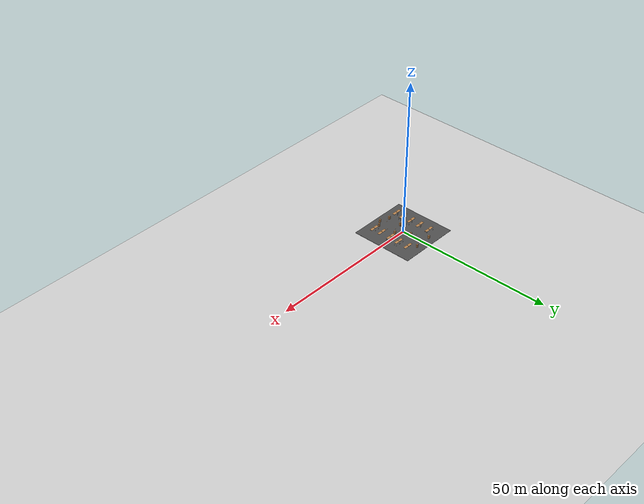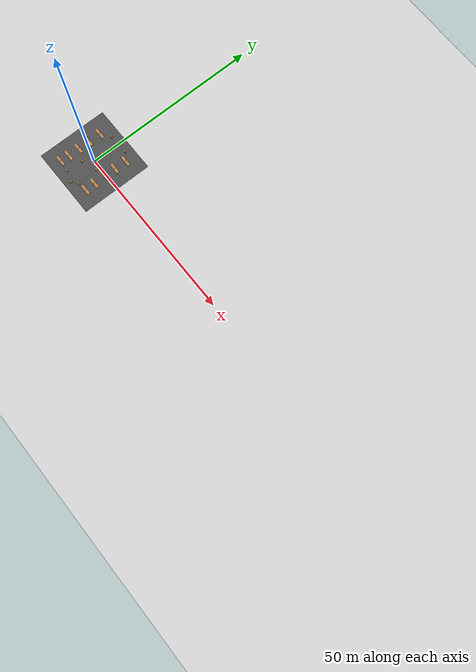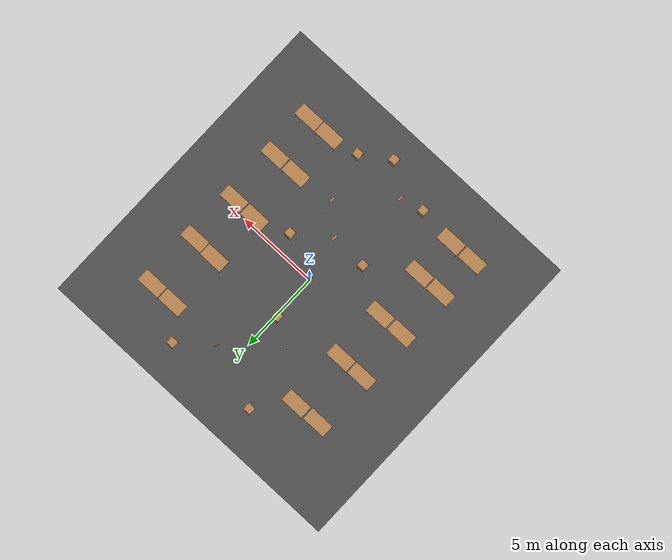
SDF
<sdf version="1.7">
 <world name="default">
  <light name="sun" type="directional">
   <pose>0 0 10 0 -0 0</pose>
   <diffuse>0.8 0.8 0.8 1</diffuse>
   <specular>0.2 0.2 0.2 1</specular>
   <attenuation>
    <range>1000</range>
    <constant>0.9</constant>
    <linear>0.01</linear>
    <quadratic>0.001</quadratic>
   </attenuation>
   <direction>-0.5 0.1 -0.9</direction>
   <spot><inner_angle>0</inner_angle><outer_angle>0</outer_angle><falloff>0</falloff></spot>
  </light>
  <model name="ground_plane">
   <static>1</static>
   <link name="link">
    <collision name="collision">
     <geometry><plane><normal>0 0 1</normal><size>100 100</size></plane></geometry>
     <surface>
      <contact><collide_bitmask>65535</collide_bitmask></contact>
      <friction><ode><mu>100</mu><mu2>50</mu2></ode></friction>
     </surface>
    </collision>
    <visual name="visual">
     <cast_shadows>0</cast_shadows>
     <geometry><plane><normal>0 0 1</normal><size>100 100</size></plane></geometry>
     <material>
      <script><uri>file://media/materials/scripts/gazebo.material</uri><name>Gazebo/Grey</name></script>
     </material>
    </visual>
   </link>
  </model>
  <gravity>0 0 -9.8</gravity>
  <magnetic_field>6e-06 2.3e-05 -4.2e-05</magnetic_field>
  <atmosphere type="adiabatic"/>
  <physics type="ode">
   <max_step_size>0.001</max_step_size>
   <real_time_factor>1</real_time_factor>
   <real_time_update_rate>1000</real_time_update_rate>
  </physics>
  <scene><ambient>0.4 0.4 0.4 1</ambient><background>0.7 0.7 0.7 1</background><shadows>1</shadows></scene>
  <audio><device>default</device></audio>
  <spherical_coordinates>
   <surface_model>EARTH_WGS84</surface_model>
   <latitude_deg>0</latitude_deg>
   <longitude_deg>0</longitude_deg>
   <elevation>0</elevation>
   <heading_deg>0</heading_deg>
  </spherical_coordinates>
  <model name="asphalt_plane">
   <static>1</static>
   <link name="link">
    <collision name="collision"><geometry><box><size>20 20 0.1</size></box></geometry></collision>
    <visual name="visual">
     <cast_shadows>0</cast_shadows>
     <geometry><box><size>20 20 0.1</size></box></geometry>
     <material>
      <script>
       <uri>model://asphalt_plane/materials/scripts</uri>
       <uri>model://asphalt_plane/materials/textures</uri>
       <name>vrc/asphalt</name>
      </script>
     </material>
    </visual>
   </link>
   <pose>0.032164 -0.016772 0 0 -0 0</pose>
  </model>
  <model name="table">
   <static>1</static>
   <link name="link">
    <collision name="surface">
     <pose>0 0 1 0 -0 0</pose>
     <geometry><box><size>1.5 0.8 0.03</size></box></geometry>
     <surface><friction><ode><mu>0.6</mu><mu2>0.6</mu2></ode></friction></surface>
    </collision>
    <visual name="visual1">
     <pose>0 0 1 0 -0 0</pose>
     <geometry><box><size>1.5 0.8 0.03</size></box></geometry>
     <material>
      <script><uri>file://media/materials/scripts/gazebo.material</uri><name>Gazebo/Wood</name></script>
     </material>
    </visual>
    <collision name="front_left_leg">
     <pose>0.68 0.38 0.5 0 -0 0</pose>
     <geometry><cylinder><radius>0.02</radius><length>1</length></cylinder></geometry>
    </collision>
    <visual name="front_left_leg">
     <pose>0.68 0.38 0.5 0 -0 0</pose>
     <geometry><cylinder><radius>0.02</radius><length>1</length></cylinder></geometry>
     <material>
      <script><uri>file://media/materials/scripts/gazebo.material</uri><name>Gazebo/Grey</name></script>
     </material>
    </visual>
    <collision name="front_right_leg">
     <pose>0.68 -0.38 0.5 0 -0 0</pose>
     <geometry><cylinder><radius>0.02</radius><length>1</length></cylinder></geometry>
    </collision>
    <visual name="front_right_leg">
     <pose>0.68 -0.38 0.5 0 -0 0</pose>
     <geometry><cylinder><radius>0.02</radius><length>1</length></cylinder></geometry>
     <material>
      <script><uri>file://media/materials/scripts/gazebo.material</uri><name>Gazebo/Grey</name></script>
     </material>
    </visual>
    <collision name="back_right_leg">
     <pose>-0.68 -0.38 0.5 0 -0 0</pose>
     <geometry><cylinder><radius>0.02</radius><length>1</length></cylinder></geometry>
    </collision>
    <visual name="back_right_leg">
     <pose>-0.68 -0.38 0.5 0 -0 0</pose>
     <geometry><cylinder><radius>0.02</radius><length>1</length></cylinder></geometry>
     <material>
      <script><uri>file://media/materials/scripts/gazebo.material</uri><name>Gazebo/Grey</name></script>
     </material>
    </visual>
    <collision name="back_left_leg">
     <pose>-0.68 0.38 0.5 0 -0 0</pose>
     <geometry><cylinder><radius>0.02</radius><length>1</length></cylinder></geometry>
    </collision>
    <visual name="back_left_leg">
     <pose>-0.68 0.38 0.5 0 -0 0</pose>
     <geometry><cylinder><radius>0.02</radius><length>1</length></cylinder></geometry>
     <material>
      <script><uri>file://media/materials/scripts/gazebo.material</uri><name>Gazebo/Grey</name></script>
     </material>
    </visual>
   </link>
   <pose>6.21309 -6.63015 0 0 -0 0</pose>
  </model>
  <model name="table_0">
   <static>1</static>
   <link name="link">
    <collision name="surface">
     <pose>0 0 1 0 -0 0</pose>
     <geometry><box><size>1.5 0.8 0.03</size></box></geometry>
     <surface><friction><ode><mu>0.6</mu><mu2>0.6</mu2></ode></friction></surface>
    </collision>
    <visual name="visual1">
     <pose>0 0 1 0 -0 0</pose>
     <geometry><box><size>1.5 0.8 0.03</size></box></geometry>
     <material>
      <script><uri>file://media/materials/scripts/gazebo.material</uri><name>Gazebo/Wood</name></script>
     </material>
    </visual>
    <collision name="front_left_leg">
     <pose>0.68 0.38 0.5 0 -0 0</pose>
     <geometry><cylinder><radius>0.02</radius><length>1</length></cylinder></geometry>
    </collision>
    <visual name="front_left_leg">
     <pose>0.68 0.38 0.5 0 -0 0</pose>
     <geometry><cylinder><radius>0.02</radius><length>1</length></cylinder></geometry>
     <material>
      <script><uri>file://media/materials/scripts/gazebo.material</uri><name>Gazebo/Grey</name></script>
     </material>
    </visual>
    <collision name="front_right_leg">
     <pose>0.68 -0.38 0.5 0 -0 0</pose>
     <geometry><cylinder><radius>0.02</radius><length>1</length></cylinder></geometry>
    </collision>
    <visual name="front_right_leg">
     <pose>0.68 -0.38 0.5 0 -0 0</pose>
     <geometry><cylinder><radius>0.02</radius><length>1</length></cylinder></geometry>
     <material>
      <script><uri>file://media/materials/scripts/gazebo.material</uri><name>Gazebo/Grey</name></script>
     </material>
    </visual>
    <collision name="back_right_leg">
     <pose>-0.68 -0.38 0.5 0 -0 0</pose>
     <geometry><cylinder><radius>0.02</radius><length>1</length></cylinder></geometry>
    </collision>
    <visual name="back_right_leg">
     <pose>-0.68 -0.38 0.5 0 -0 0</pose>
     <geometry><cylinder><radius>0.02</radius><length>1</length></cylinder></geometry>
     <material>
      <script><uri>file://media/materials/scripts/gazebo.material</uri><name>Gazebo/Grey</name></script>
     </material>
    </visual>
    <collision name="back_left_leg">
     <pose>-0.68 0.38 0.5 0 -0 0</pose>
     <geometry><cylinder><radius>0.02</radius><length>1</length></cylinder></geometry>
    </collision>
    <visual name="back_left_leg">
     <pose>-0.68 0.38 0.5 0 -0 0</pose>
     <geometry><cylinder><radius>0.02</radius><length>1</length></cylinder></geometry>
     <material>
      <script><uri>file://media/materials/scripts/gazebo.material</uri><name>Gazebo/Grey</name></script>
     </material>
    </visual>
   </link>
   <pose>6.15369 -3.77587 0 0 -0 0</pose>
  </model>
  <model name="table_1">
   <static>1</static>
   <link name="link">
    <collision name="surface">
     <pose>0 0 1 0 -0 0</pose>
     <geometry><box><size>1.5 0.8 0.03</size></box></geometry>
     <surface><friction><ode><mu>0.6</mu><mu2>0.6</mu2></ode></friction></surface>
    </collision>
    <visual name="visual1">
     <pose>0 0 1 0 -0 0</pose>
     <geometry><box><size>1.5 0.8 0.03</size></box></geometry>
     <material>
      <script><uri>file://media/materials/scripts/gazebo.material</uri><name>Gazebo/Wood</name></script>
     </material>
    </visual>
    <collision name="front_left_leg">
     <pose>0.68 0.38 0.5 0 -0 0</pose>
     <geometry><cylinder><radius>0.02</radius><length>1</length></cylinder></geometry>
    </collision>
    <visual name="front_left_leg">
     <pose>0.68 0.38 0.5 0 -0 0</pose>
     <geometry><cylinder><radius>0.02</radius><length>1</length></cylinder></geometry>
     <material>
      <script><uri>file://media/materials/scripts/gazebo.material</uri><name>Gazebo/Grey</name></script>
     </material>
    </visual>
    <collision name="front_right_leg">
     <pose>0.68 -0.38 0.5 0 -0 0</pose>
     <geometry><cylinder><radius>0.02</radius><length>1</length></cylinder></geometry>
    </collision>
    <visual name="front_right_leg">
     <pose>0.68 -0.38 0.5 0 -0 0</pose>
     <geometry><cylinder><radius>0.02</radius><length>1</length></cylinder></geometry>
     <material>
      <script><uri>file://media/materials/scripts/gazebo.material</uri><name>Gazebo/Grey</name></script>
     </material>
    </visual>
    <collision name="back_right_leg">
     <pose>-0.68 -0.38 0.5 0 -0 0</pose>
     <geometry><cylinder><radius>0.02</radius><length>1</length></cylinder></geometry>
    </collision>
    <visual name="back_right_leg">
     <pose>-0.68 -0.38 0.5 0 -0 0</pose>
     <geometry><cylinder><radius>0.02</radius><length>1</length></cylinder></geometry>
     <material>
      <script><uri>file://media/materials/scripts/gazebo.material</uri><name>Gazebo/Grey</name></script>
     </material>
    </visual>
    <collision name="back_left_leg">
     <pose>-0.68 0.38 0.5 0 -0 0</pose>
     <geometry><cylinder><radius>0.02</radius><length>1</length></cylinder></geometry>
    </collision>
    <visual name="back_left_leg">
     <pose>-0.68 0.38 0.5 0 -0 0</pose>
     <geometry><cylinder><radius>0.02</radius><length>1</length></cylinder></geometry>
     <material>
      <script><uri>file://media/materials/scripts/gazebo.material</uri><name>Gazebo/Grey</name></script>
     </material>
    </visual>
   </link>
   <pose>6.14482 -0.397258 0 0 -0 0</pose>
  </model>
  <model name="table_2">
   <static>1</static>
   <link name="link">
    <collision name="surface">
     <pose>0 0 1 0 -0 0</pose>
     <geometry><box><size>1.5 0.8 0.03</size></box></geometry>
     <surface><friction><ode><mu>0.6</mu><mu2>0.6</mu2></ode></friction></surface>
    </collision>
    <visual name="visual1">
     <pose>0 0 1 0 -0 0</pose>
     <geometry><box><size>1.5 0.8 0.03</size></box></geometry>
     <material>
      <script><uri>file://media/materials/scripts/gazebo.material</uri><name>Gazebo/Wood</name></script>
     </material>
    </visual>
    <collision name="front_left_leg">
     <pose>0.68 0.38 0.5 0 -0 0</pose>
     <geometry><cylinder><radius>0.02</radius><length>1</length></cylinder></geometry>
    </collision>
    <visual name="front_left_leg">
     <pose>0.68 0.38 0.5 0 -0 0</pose>
     <geometry><cylinder><radius>0.02</radius><length>1</length></cylinder></geometry>
     <material>
      <script><uri>file://media/materials/scripts/gazebo.material</uri><name>Gazebo/Grey</name></script>
     </material>
    </visual>
    <collision name="front_right_leg">
     <pose>0.68 -0.38 0.5 0 -0 0</pose>
     <geometry><cylinder><radius>0.02</radius><length>1</length></cylinder></geometry>
    </collision>
    <visual name="front_right_leg">
     <pose>0.68 -0.38 0.5 0 -0 0</pose>
     <geometry><cylinder><radius>0.02</radius><length>1</length></cylinder></geometry>
     <material>
      <script><uri>file://media/materials/scripts/gazebo.material</uri><name>Gazebo/Grey</name></script>
     </material>
    </visual>
    <collision name="back_right_leg">
     <pose>-0.68 -0.38 0.5 0 -0 0</pose>
     <geometry><cylinder><radius>0.02</radius><length>1</length></cylinder></geometry>
    </collision>
    <visual name="back_right_leg">
     <pose>-0.68 -0.38 0.5 0 -0 0</pose>
     <geometry><cylinder><radius>0.02</radius><length>1</length></cylinder></geometry>
     <material>
      <script><uri>file://media/materials/scripts/gazebo.material</uri><name>Gazebo/Grey</name></script>
     </material>
    </visual>
    <collision name="back_left_leg">
     <pose>-0.68 0.38 0.5 0 -0 0</pose>
     <geometry><cylinder><radius>0.02</radius><length>1</length></cylinder></geometry>
    </collision>
    <visual name="back_left_leg">
     <pose>-0.68 0.38 0.5 0 -0 0</pose>
     <geometry><cylinder><radius>0.02</radius><length>1</length></cylinder></geometry>
     <material>
      <script><uri>file://media/materials/scripts/gazebo.material</uri><name>Gazebo/Grey</name></script>
     </material>
    </visual>
   </link>
   <pose>6.21479 2.74506 0 0 -0 0</pose>
  </model>
  <model name="table_3">
   <static>1</static>
   <link name="link">
    <collision name="surface">
     <pose>0 0 1 0 -0 0</pose>
     <geometry><box><size>1.5 0.8 0.03</size></box></geometry>
     <surface><friction><ode><mu>0.6</mu><mu2>0.6</mu2></ode></friction></surface>
    </collision>
    <visual name="visual1">
     <pose>0 0 1 0 -0 0</pose>
     <geometry><box><size>1.5 0.8 0.03</size></box></geometry>
     <material>
      <script><uri>file://media/materials/scripts/gazebo.material</uri><name>Gazebo/Wood</name></script>
     </material>
    </visual>
    <collision name="front_left_leg">
     <pose>0.68 0.38 0.5 0 -0 0</pose>
     <geometry><cylinder><radius>0.02</radius><length>1</length></cylinder></geometry>
    </collision>
    <visual name="front_left_leg">
     <pose>0.68 0.38 0.5 0 -0 0</pose>
     <geometry><cylinder><radius>0.02</radius><length>1</length></cylinder></geometry>
     <material>
      <script><uri>file://media/materials/scripts/gazebo.material</uri><name>Gazebo/Grey</name></script>
     </material>
    </visual>
    <collision name="front_right_leg">
     <pose>0.68 -0.38 0.5 0 -0 0</pose>
     <geometry><cylinder><radius>0.02</radius><length>1</length></cylinder></geometry>
    </collision>
    <visual name="front_right_leg">
     <pose>0.68 -0.38 0.5 0 -0 0</pose>
     <geometry><cylinder><radius>0.02</radius><length>1</length></cylinder></geometry>
     <material>
      <script><uri>file://media/materials/scripts/gazebo.material</uri><name>Gazebo/Grey</name></script>
     </material>
    </visual>
    <collision name="back_right_leg">
     <pose>-0.68 -0.38 0.5 0 -0 0</pose>
     <geometry><cylinder><radius>0.02</radius><length>1</length></cylinder></geometry>
    </collision>
    <visual name="back_right_leg">
     <pose>-0.68 -0.38 0.5 0 -0 0</pose>
     <geometry><cylinder><radius>0.02</radius><length>1</length></cylinder></geometry>
     <material>
      <script><uri>file://media/materials/scripts/gazebo.material</uri><name>Gazebo/Grey</name></script>
     </material>
    </visual>
    <collision name="back_left_leg">
     <pose>-0.68 0.38 0.5 0 -0 0</pose>
     <geometry><cylinder><radius>0.02</radius><length>1</length></cylinder></geometry>
    </collision>
    <visual name="back_left_leg">
     <pose>-0.68 0.38 0.5 0 -0 0</pose>
     <geometry><cylinder><radius>0.02</radius><length>1</length></cylinder></geometry>
     <material>
      <script><uri>file://media/materials/scripts/gazebo.material</uri><name>Gazebo/Grey</name></script>
     </material>
    </visual>
   </link>
   <pose>6.23168 6.20143 0 0 -0 0</pose>
  </model>
  <model name="table_4">
   <static>1</static>
   <link name="link">
    <collision name="surface">
     <pose>0 0 1 0 -0 0</pose>
     <geometry><box><size>1.5 0.8 0.03</size></box></geometry>
     <surface><friction><ode><mu>0.6</mu><mu2>0.6</mu2></ode></friction></surface>
    </collision>
    <visual name="visual1">
     <pose>0 0 1 0 -0 0</pose>
     <geometry><box><size>1.5 0.8 0.03</size></box></geometry>
     <material>
      <script><uri>file://media/materials/scripts/gazebo.material</uri><name>Gazebo/Wood</name></script>
     </material>
    </visual>
    <collision name="front_left_leg">
     <pose>0.68 0.38 0.5 0 -0 0</pose>
     <geometry><cylinder><radius>0.02</radius><length>1</length></cylinder></geometry>
    </collision>
    <visual name="front_left_leg">
     <pose>0.68 0.38 0.5 0 -0 0</pose>
     <geometry><cylinder><radius>0.02</radius><length>1</length></cylinder></geometry>
     <material>
      <script><uri>file://media/materials/scripts/gazebo.material</uri><name>Gazebo/Grey</name></script>
     </material>
    </visual>
    <collision name="front_right_leg">
     <pose>0.68 -0.38 0.5 0 -0 0</pose>
     <geometry><cylinder><radius>0.02</radius><length>1</length></cylinder></geometry>
    </collision>
    <visual name="front_right_leg">
     <pose>0.68 -0.38 0.5 0 -0 0</pose>
     <geometry><cylinder><radius>0.02</radius><length>1</length></cylinder></geometry>
     <material>
      <script><uri>file://media/materials/scripts/gazebo.material</uri><name>Gazebo/Grey</name></script>
     </material>
    </visual>
    <collision name="back_right_leg">
     <pose>-0.68 -0.38 0.5 0 -0 0</pose>
     <geometry><cylinder><radius>0.02</radius><length>1</length></cylinder></geometry>
    </collision>
    <visual name="back_right_leg">
     <pose>-0.68 -0.38 0.5 0 -0 0</pose>
     <geometry><cylinder><radius>0.02</radius><length>1</length></cylinder></geometry>
     <material>
      <script><uri>file://media/materials/scripts/gazebo.material</uri><name>Gazebo/Grey</name></script>
     </material>
    </visual>
    <collision name="back_left_leg">
     <pose>-0.68 0.38 0.5 0 -0 0</pose>
     <geometry><cylinder><radius>0.02</radius><length>1</length></cylinder></geometry>
    </collision>
    <visual name="back_left_leg">
     <pose>-0.68 0.38 0.5 0 -0 0</pose>
     <geometry><cylinder><radius>0.02</radius><length>1</length></cylinder></geometry>
     <material>
      <script><uri>file://media/materials/scripts/gazebo.material</uri><name>Gazebo/Grey</name></script>
     </material>
    </visual>
   </link>
   <pose>-5.982 -6.93187 0 0 -0 0</pose>
  </model>
  <model name="table_5">
   <static>1</static>
   <link name="link">
    <collision name="surface">
     <pose>0 0 1 0 -0 0</pose>
     <geometry><box><size>1.5 0.8 0.03</size></box></geometry>
     <surface><friction><ode><mu>0.6</mu><mu2>0.6</mu2></ode></friction></surface>
    </collision>
    <visual name="visual1">
     <pose>0 0 1 0 -0 0</pose>
     <geometry><box><size>1.5 0.8 0.03</size></box></geometry>
     <material>
      <script><uri>file://media/materials/scripts/gazebo.material</uri><name>Gazebo/Wood</name></script>
     </material>
    </visual>
    <collision name="front_left_leg">
     <pose>0.68 0.38 0.5 0 -0 0</pose>
     <geometry><cylinder><radius>0.02</radius><length>1</length></cylinder></geometry>
    </collision>
    <visual name="front_left_leg">
     <pose>0.68 0.38 0.5 0 -0 0</pose>
     <geometry><cylinder><radius>0.02</radius><length>1</length></cylinder></geometry>
     <material>
      <script><uri>file://media/materials/scripts/gazebo.material</uri><name>Gazebo/Grey</name></script>
     </material>
    </visual>
    <collision name="front_right_leg">
     <pose>0.68 -0.38 0.5 0 -0 0</pose>
     <geometry><cylinder><radius>0.02</radius><length>1</length></cylinder></geometry>
    </collision>
    <visual name="front_right_leg">
     <pose>0.68 -0.38 0.5 0 -0 0</pose>
     <geometry><cylinder><radius>0.02</radius><length>1</length></cylinder></geometry>
     <material>
      <script><uri>file://media/materials/scripts/gazebo.material</uri><name>Gazebo/Grey</name></script>
     </material>
    </visual>
    <collision name="back_right_leg">
     <pose>-0.68 -0.38 0.5 0 -0 0</pose>
     <geometry><cylinder><radius>0.02</radius><length>1</length></cylinder></geometry>
    </collision>
    <visual name="back_right_leg">
     <pose>-0.68 -0.38 0.5 0 -0 0</pose>
     <geometry><cylinder><radius>0.02</radius><length>1</length></cylinder></geometry>
     <material>
      <script><uri>file://media/materials/scripts/gazebo.material</uri><name>Gazebo/Grey</name></script>
     </material>
    </visual>
    <collision name="back_left_leg">
     <pose>-0.68 0.38 0.5 0 -0 0</pose>
     <geometry><cylinder><radius>0.02</radius><length>1</length></cylinder></geometry>
    </collision>
    <visual name="back_left_leg">
     <pose>-0.68 0.38 0.5 0 -0 0</pose>
     <geometry><cylinder><radius>0.02</radius><length>1</length></cylinder></geometry>
     <material>
      <script><uri>file://media/materials/scripts/gazebo.material</uri><name>Gazebo/Grey</name></script>
     </material>
    </visual>
   </link>
   <pose>-5.90789 -4.39985 0 0 -0 0</pose>
  </model>
  <model name="table_6">
   <static>1</static>
   <link name="link">
    <collision name="surface">
     <pose>0 0 1 0 -0 0</pose>
     <geometry><box><size>1.5 0.8 0.03</size></box></geometry>
     <surface><friction><ode><mu>0.6</mu><mu2>0.6</mu2></ode></friction></surface>
    </collision>
    <visual name="visual1">
     <pose>0 0 1 0 -0 0</pose>
     <geometry><box><size>1.5 0.8 0.03</size></box></geometry>
     <material>
      <script><uri>file://media/materials/scripts/gazebo.material</uri><name>Gazebo/Wood</name></script>
     </material>
    </visual>
    <collision name="front_left_leg">
     <pose>0.68 0.38 0.5 0 -0 0</pose>
     <geometry><cylinder><radius>0.02</radius><length>1</length></cylinder></geometry>
    </collision>
    <visual name="front_left_leg">
     <pose>0.68 0.38 0.5 0 -0 0</pose>
     <geometry><cylinder><radius>0.02</radius><length>1</length></cylinder></geometry>
     <material>
      <script><uri>file://media/materials/scripts/gazebo.material</uri><name>Gazebo/Grey</name></script>
     </material>
    </visual>
    <collision name="front_right_leg">
     <pose>0.68 -0.38 0.5 0 -0 0</pose>
     <geometry><cylinder><radius>0.02</radius><length>1</length></cylinder></geometry>
    </collision>
    <visual name="front_right_leg">
     <pose>0.68 -0.38 0.5 0 -0 0</pose>
     <geometry><cylinder><radius>0.02</radius><length>1</length></cylinder></geometry>
     <material>
      <script><uri>file://media/materials/scripts/gazebo.material</uri><name>Gazebo/Grey</name></script>
     </material>
    </visual>
    <collision name="back_right_leg">
     <pose>-0.68 -0.38 0.5 0 -0 0</pose>
     <geometry><cylinder><radius>0.02</radius><length>1</length></cylinder></geometry>
    </collision>
    <visual name="back_right_leg">
     <pose>-0.68 -0.38 0.5 0 -0 0</pose>
     <geometry><cylinder><radius>0.02</radius><length>1</length></cylinder></geometry>
     <material>
      <script><uri>file://media/materials/scripts/gazebo.material</uri><name>Gazebo/Grey</name></script>
     </material>
    </visual>
    <collision name="back_left_leg">
     <pose>-0.68 0.38 0.5 0 -0 0</pose>
     <geometry><cylinder><radius>0.02</radius><length>1</length></cylinder></geometry>
    </collision>
    <visual name="back_left_leg">
     <pose>-0.68 0.38 0.5 0 -0 0</pose>
     <geometry><cylinder><radius>0.02</radius><length>1</length></cylinder></geometry>
     <material>
      <script><uri>file://media/materials/scripts/gazebo.material</uri><name>Gazebo/Grey</name></script>
     </material>
    </visual>
   </link>
   <pose>-5.86238 -1.22885 0 0 -0 0</pose>
  </model>
  <model name="table_7">
   <static>1</static>
   <link name="link">
    <collision name="surface">
     <pose>0 0 1 0 -0 0</pose>
     <geometry><box><size>1.5 0.8 0.03</size></box></geometry>
     <surface><friction><ode><mu>0.6</mu><mu2>0.6</mu2></ode></friction></surface>
    </collision>
    <visual name="visual1">
     <pose>0 0 1 0 -0 0</pose>
     <geometry><box><size>1.5 0.8 0.03</size></box></geometry>
     <material>
      <script><uri>file://media/materials/scripts/gazebo.material</uri><name>Gazebo/Wood</name></script>
     </material>
    </visual>
    <collision name="front_left_leg">
     <pose>0.68 0.38 0.5 0 -0 0</pose>
     <geometry><cylinder><radius>0.02</radius><length>1</length></cylinder></geometry>
    </collision>
    <visual name="front_left_leg">
     <pose>0.68 0.38 0.5 0 -0 0</pose>
     <geometry><cylinder><radius>0.02</radius><length>1</length></cylinder></geometry>
     <material>
      <script><uri>file://media/materials/scripts/gazebo.material</uri><name>Gazebo/Grey</name></script>
     </material>
    </visual>
    <collision name="front_right_leg">
     <pose>0.68 -0.38 0.5 0 -0 0</pose>
     <geometry><cylinder><radius>0.02</radius><length>1</length></cylinder></geometry>
    </collision>
    <visual name="front_right_leg">
     <pose>0.68 -0.38 0.5 0 -0 0</pose>
     <geometry><cylinder><radius>0.02</radius><length>1</length></cylinder></geometry>
     <material>
      <script><uri>file://media/materials/scripts/gazebo.material</uri><name>Gazebo/Grey</name></script>
     </material>
    </visual>
    <collision name="back_right_leg">
     <pose>-0.68 -0.38 0.5 0 -0 0</pose>
     <geometry><cylinder><radius>0.02</radius><length>1</length></cylinder></geometry>
    </collision>
    <visual name="back_right_leg">
     <pose>-0.68 -0.38 0.5 0 -0 0</pose>
     <geometry><cylinder><radius>0.02</radius><length>1</length></cylinder></geometry>
     <material>
      <script><uri>file://media/materials/scripts/gazebo.material</uri><name>Gazebo/Grey</name></script>
     </material>
    </visual>
    <collision name="back_left_leg">
     <pose>-0.68 0.38 0.5 0 -0 0</pose>
     <geometry><cylinder><radius>0.02</radius><length>1</length></cylinder></geometry>
    </collision>
    <visual name="back_left_leg">
     <pose>-0.68 0.38 0.5 0 -0 0</pose>
     <geometry><cylinder><radius>0.02</radius><length>1</length></cylinder></geometry>
     <material>
      <script><uri>file://media/materials/scripts/gazebo.material</uri><name>Gazebo/Grey</name></script>
     </material>
    </visual>
   </link>
   <pose>-5.87096 2.0486 0 0 -0 0</pose>
  </model>
  <model name="table_8">
   <static>1</static>
   <link name="link">
    <collision name="surface">
     <pose>0 0 1 0 -0 0</pose>
     <geometry><box><size>1.5 0.8 0.03</size></box></geometry>
     <surface><friction><ode><mu>0.6</mu><mu2>0.6</mu2></ode></friction></surface>
    </collision>
    <visual name="visual1">
     <pose>0 0 1 0 -0 0</pose>
     <geometry><box><size>1.5 0.8 0.03</size></box></geometry>
     <material>
      <script><uri>file://media/materials/scripts/gazebo.material</uri><name>Gazebo/Wood</name></script>
     </material>
    </visual>
    <collision name="front_left_leg">
     <pose>0.68 0.38 0.5 0 -0 0</pose>
     <geometry><cylinder><radius>0.02</radius><length>1</length></cylinder></geometry>
    </collision>
    <visual name="front_left_leg">
     <pose>0.68 0.38 0.5 0 -0 0</pose>
     <geometry><cylinder><radius>0.02</radius><length>1</length></cylinder></geometry>
     <material>
      <script><uri>file://media/materials/scripts/gazebo.material</uri><name>Gazebo/Grey</name></script>
     </material>
    </visual>
    <collision name="front_right_leg">
     <pose>0.68 -0.38 0.5 0 -0 0</pose>
     <geometry><cylinder><radius>0.02</radius><length>1</length></cylinder></geometry>
    </collision>
    <visual name="front_right_leg">
     <pose>0.68 -0.38 0.5 0 -0 0</pose>
     <geometry><cylinder><radius>0.02</radius><length>1</length></cylinder></geometry>
     <material>
      <script><uri>file://media/materials/scripts/gazebo.material</uri><name>Gazebo/Grey</name></script>
     </material>
    </visual>
    <collision name="back_right_leg">
     <pose>-0.68 -0.38 0.5 0 -0 0</pose>
     <geometry><cylinder><radius>0.02</radius><length>1</length></cylinder></geometry>
    </collision>
    <visual name="back_right_leg">
     <pose>-0.68 -0.38 0.5 0 -0 0</pose>
     <geometry><cylinder><radius>0.02</radius><length>1</length></cylinder></geometry>
     <material>
      <script><uri>file://media/materials/scripts/gazebo.material</uri><name>Gazebo/Grey</name></script>
     </material>
    </visual>
    <collision name="back_left_leg">
     <pose>-0.68 0.38 0.5 0 -0 0</pose>
     <geometry><cylinder><radius>0.02</radius><length>1</length></cylinder></geometry>
    </collision>
    <visual name="back_left_leg">
     <pose>-0.68 0.38 0.5 0 -0 0</pose>
     <geometry><cylinder><radius>0.02</radius><length>1</length></cylinder></geometry>
     <material>
      <script><uri>file://media/materials/scripts/gazebo.material</uri><name>Gazebo/Grey</name></script>
     </material>
    </visual>
   </link>
   <pose>-5.82635 5.59166 0 0 -0 0</pose>
  </model>
  <model name="cabinet">
   <static>1</static>
   <link name="cabinet_bottom_plate">
    <inertial>
     <pose>0 0 -1 0 -0 0</pose>
     <inertia><ixx>2.05</ixx><ixy>0</ixy><ixz>0</ixz><iyy>2.05</iyy><iyz>0</iyz><izz>2.05</izz></inertia>
     <mass>25</mass>
    </inertial>
    <collision name="cabinet_bottom_plate_geom">
     <pose>0 0 0.01 0 -0 0</pose>
     <geometry><box><size>0.45 0.45 0.02</size></box></geometry>
    </collision>
    <visual name="cabinet_bottom_plate_geom_visual">
     <pose>0 0 0.01 0 -0 0</pose>
     <geometry><box><size>0.45 0.45 0.02</size></box></geometry>
     <material>
      <script><uri>file://media/materials/scripts/gazebo.material</uri><name>Gazebo/Wood</name></script>
     </material>
    </visual>
    <collision name="cabinet_bottom_plate_geom_cabinet_back_plate">
     <pose>0.235 0 0.51 0 -0 0</pose>
     <geometry><box><size>0.02 0.45 1.02</size></box></geometry>
    </collision>
    <visual name="cabinet_bottom_plate_geom_cabinet_back_plate_visual">
     <pose>0.235 0 0.51 0 -0 0</pose>
     <geometry><box><size>0.02 0.45 1.02</size></box></geometry>
     <material>
      <script><uri>file://media/materials/scripts/gazebo.material</uri><name>Gazebo/Wood</name></script>
     </material>
    </visual>
    <collision name="cabinet_bottom_plate_geom_cabinet_left_plate">
     <pose>0 0.235 0.51 0 -0 0</pose>
     <geometry><box><size>0.45 0.02 1.02</size></box></geometry>
    </collision>
    <visual name="cabinet_bottom_plate_geom_cabinet_left_plate_visual">
     <pose>0 0.235 0.51 0 -0 0</pose>
     <geometry><box><size>0.45 0.02 1.02</size></box></geometry>
     <material>
      <script><uri>file://media/materials/scripts/gazebo.material</uri><name>Gazebo/Wood</name></script>
     </material>
    </visual>
    <collision name="cabinet_bottom_plate_geom_cabinet_middle_plate">
     <pose>0 0 0.51 0 -0 0</pose>
     <geometry><box><size>0.45 0.45 0.02</size></box></geometry>
    </collision>
    <visual name="cabinet_bottom_plate_geom_cabinet_middle_plate_visual">
     <pose>0 0 0.51 0 -0 0</pose>
     <geometry><box><size>0.45 0.45 0.02</size></box></geometry>
     <material>
      <script><uri>file://media/materials/scripts/gazebo.material</uri><name>Gazebo/Wood</name></script>
     </material>
    </visual>
    <collision name="cabinet_bottom_plate_geom_cabinet_right_plate">
     <pose>0 -0.235 0.51 0 -0 0</pose>
     <geometry><box><size>0.45 0.02 1.02</size></box></geometry>
    </collision>
    <visual name="cabinet_bottom_plate_geom_cabinet_right_plate_visual">
     <pose>0 -0.235 0.51 0 -0 0</pose>
     <geometry><box><size>0.45 0.02 1.02</size></box></geometry>
     <material>
      <script><uri>file://media/materials/scripts/gazebo.material</uri><name>Gazebo/Wood</name></script>
     </material>
    </visual>
    <collision name="cabinet_bottom_plate_geom_cabinet_top_plate">
     <pose>0 0 1.01 0 -0 0</pose>
     <geometry><box><size>0.45 0.45 0.02</size></box></geometry>
    </collision>
    <visual name="cabinet_bottom_plate_geom_cabinet_top_plate_visual">
     <pose>0 0 1.01 0 -0 0</pose>
     <geometry><box><size>0.45 0.45 0.02</size></box></geometry>
     <material>
      <script><uri>file://media/materials/scripts/gazebo.material</uri><name>Gazebo/Wood</name></script>
     </material>
    </visual>
   </link>
   <pose>-2.04611 -7.14064 0 0 -0 0</pose>
  </model>
  <model name="cabinet_0">
   <static>1</static>
   <link name="cabinet_bottom_plate">
    <inertial>
     <pose>0 0 -1 0 -0 0</pose>
     <inertia><ixx>2.05</ixx><ixy>0</ixy><ixz>0</ixz><iyy>2.05</iyy><iyz>0</iyz><izz>2.05</izz></inertia>
     <mass>25</mass>
    </inertial>
    <collision name="cabinet_bottom_plate_geom">
     <pose>0 0 0.01 0 -0 0</pose>
     <geometry><box><size>0.45 0.45 0.02</size></box></geometry>
    </collision>
    <visual name="cabinet_bottom_plate_geom_visual">
     <pose>0 0 0.01 0 -0 0</pose>
     <geometry><box><size>0.45 0.45 0.02</size></box></geometry>
     <material>
      <script><uri>file://media/materials/scripts/gazebo.material</uri><name>Gazebo/Wood</name></script>
     </material>
    </visual>
    <collision name="cabinet_bottom_plate_geom_cabinet_back_plate">
     <pose>0.235 0 0.51 0 -0 0</pose>
     <geometry><box><size>0.02 0.45 1.02</size></box></geometry>
    </collision>
    <visual name="cabinet_bottom_plate_geom_cabinet_back_plate_visual">
     <pose>0.235 0 0.51 0 -0 0</pose>
     <geometry><box><size>0.02 0.45 1.02</size></box></geometry>
     <material>
      <script><uri>file://media/materials/scripts/gazebo.material</uri><name>Gazebo/Wood</name></script>
     </material>
    </visual>
    <collision name="cabinet_bottom_plate_geom_cabinet_left_plate">
     <pose>0 0.235 0.51 0 -0 0</pose>
     <geometry><box><size>0.45 0.02 1.02</size></box></geometry>
    </collision>
    <visual name="cabinet_bottom_plate_geom_cabinet_left_plate_visual">
     <pose>0 0.235 0.51 0 -0 0</pose>
     <geometry><box><size>0.45 0.02 1.02</size></box></geometry>
     <material>
      <script><uri>file://media/materials/scripts/gazebo.material</uri><name>Gazebo/Wood</name></script>
     </material>
    </visual>
    <collision name="cabinet_bottom_plate_geom_cabinet_middle_plate">
     <pose>0 0 0.51 0 -0 0</pose>
     <geometry><box><size>0.45 0.45 0.02</size></box></geometry>
    </collision>
    <visual name="cabinet_bottom_plate_geom_cabinet_middle_plate_visual">
     <pose>0 0 0.51 0 -0 0</pose>
     <geometry><box><size>0.45 0.45 0.02</size></box></geometry>
     <material>
      <script><uri>file://media/materials/scripts/gazebo.material</uri><name>Gazebo/Wood</name></script>
     </material>
    </visual>
    <collision name="cabinet_bottom_plate_geom_cabinet_right_plate">
     <pose>0 -0.235 0.51 0 -0 0</pose>
     <geometry><box><size>0.45 0.02 1.02</size></box></geometry>
    </collision>
    <visual name="cabinet_bottom_plate_geom_cabinet_right_plate_visual">
     <pose>0 -0.235 0.51 0 -0 0</pose>
     <geometry><box><size>0.45 0.02 1.02</size></box></geometry>
     <material>
      <script><uri>file://media/materials/scripts/gazebo.material</uri><name>Gazebo/Wood</name></script>
     </material>
    </visual>
    <collision name="cabinet_bottom_plate_geom_cabinet_top_plate">
     <pose>0 0 1.01 0 -0 0</pose>
     <geometry><box><size>0.45 0.45 0.02</size></box></geometry>
    </collision>
    <visual name="cabinet_bottom_plate_geom_cabinet_top_plate_visual">
     <pose>0 0 1.01 0 -0 0</pose>
     <geometry><box><size>0.45 0.45 0.02</size></box></geometry>
     <material>
      <script><uri>file://media/materials/scripts/gazebo.material</uri><name>Gazebo/Wood</name></script>
     </material>
    </visual>
   </link>
   <pose>2.81784 -6.99702 0 0 -0 0</pose>
  </model>
  <model name="cabinet_1">
   <static>1</static>
   <link name="cabinet_bottom_plate">
    <inertial>
     <pose>0 0 -1 0 -0 0</pose>
     <inertia><ixx>2.05</ixx><ixy>0</ixy><ixz>0</ixz><iyy>2.05</iyy><iyz>0</iyz><izz>2.05</izz></inertia>
     <mass>25</mass>
    </inertial>
    <collision name="cabinet_bottom_plate_geom">
     <pose>0 0 0.01 0 -0 0</pose>
     <geometry><box><size>0.45 0.45 0.02</size></box></geometry>
    </collision>
    <visual name="cabinet_bottom_plate_geom_visual">
     <pose>0 0 0.01 0 -0 0</pose>
     <geometry><box><size>0.45 0.45 0.02</size></box></geometry>
     <material>
      <script><uri>file://media/materials/scripts/gazebo.material</uri><name>Gazebo/Wood</name></script>
     </material>
    </visual>
    <collision name="cabinet_bottom_plate_geom_cabinet_back_plate">
     <pose>0.235 0 0.51 0 -0 0</pose>
     <geometry><box><size>0.02 0.45 1.02</size></box></geometry>
    </collision>
    <visual name="cabinet_bottom_plate_geom_cabinet_back_plate_visual">
     <pose>0.235 0 0.51 0 -0 0</pose>
     <geometry><box><size>0.02 0.45 1.02</size></box></geometry>
     <material>
      <script><uri>file://media/materials/scripts/gazebo.material</uri><name>Gazebo/Wood</name></script>
     </material>
    </visual>
    <collision name="cabinet_bottom_plate_geom_cabinet_left_plate">
     <pose>0 0.235 0.51 0 -0 0</pose>
     <geometry><box><size>0.45 0.02 1.02</size></box></geometry>
    </collision>
    <visual name="cabinet_bottom_plate_geom_cabinet_left_plate_visual">
     <pose>0 0.235 0.51 0 -0 0</pose>
     <geometry><box><size>0.45 0.02 1.02</size></box></geometry>
     <material>
      <script><uri>file://media/materials/scripts/gazebo.material</uri><name>Gazebo/Wood</name></script>
     </material>
    </visual>
    <collision name="cabinet_bottom_plate_geom_cabinet_middle_plate">
     <pose>0 0 0.51 0 -0 0</pose>
     <geometry><box><size>0.45 0.45 0.02</size></box></geometry>
    </collision>
    <visual name="cabinet_bottom_plate_geom_cabinet_middle_plate_visual">
     <pose>0 0 0.51 0 -0 0</pose>
     <geometry><box><size>0.45 0.45 0.02</size></box></geometry>
     <material>
      <script><uri>file://media/materials/scripts/gazebo.material</uri><name>Gazebo/Wood</name></script>
     </material>
    </visual>
    <collision name="cabinet_bottom_plate_geom_cabinet_right_plate">
     <pose>0 -0.235 0.51 0 -0 0</pose>
     <geometry><box><size>0.45 0.02 1.02</size></box></geometry>
    </collision>
    <visual name="cabinet_bottom_plate_geom_cabinet_right_plate_visual">
     <pose>0 -0.235 0.51 0 -0 0</pose>
     <geometry><box><size>0.45 0.02 1.02</size></box></geometry>
     <material>
      <script><uri>file://media/materials/scripts/gazebo.material</uri><name>Gazebo/Wood</name></script>
     </material>
    </visual>
    <collision name="cabinet_bottom_plate_geom_cabinet_top_plate">
     <pose>0 0 1.01 0 -0 0</pose>
     <geometry><box><size>0.45 0.45 0.02</size></box></geometry>
    </collision>
    <visual name="cabinet_bottom_plate_geom_cabinet_top_plate_visual">
     <pose>0 0 1.01 0 -0 0</pose>
     <geometry><box><size>0.45 0.45 0.02</size></box></geometry>
     <material>
      <script><uri>file://media/materials/scripts/gazebo.material</uri><name>Gazebo/Wood</name></script>
     </material>
    </visual>
   </link>
   <pose>-2.51088 7.6262 0 0 -0 0</pose>
  </model>
  <model name="cabinet_2">
   <static>1</static>
   <link name="cabinet_bottom_plate">
    <inertial>
     <pose>0 0 -1 0 -0 0</pose>
     <inertia><ixx>2.05</ixx><ixy>0</ixy><ixz>0</ixz><iyy>2.05</iyy><iyz>0</iyz><izz>2.05</izz></inertia>
     <mass>25</mass>
    </inertial>
    <collision name="cabinet_bottom_plate_geom">
     <pose>0 0 0.01 0 -0 0</pose>
     <geometry><box><size>0.45 0.45 0.02</size></box></geometry>
    </collision>
    <visual name="cabinet_bottom_plate_geom_visual">
     <pose>0 0 0.01 0 -0 0</pose>
     <geometry><box><size>0.45 0.45 0.02</size></box></geometry>
     <material>
      <script><uri>file://media/materials/scripts/gazebo.material</uri><name>Gazebo/Wood</name></script>
     </material>
    </visual>
    <collision name="cabinet_bottom_plate_geom_cabinet_back_plate">
     <pose>0.235 0 0.51 0 -0 0</pose>
     <geometry><box><size>0.02 0.45 1.02</size></box></geometry>
    </collision>
    <visual name="cabinet_bottom_plate_geom_cabinet_back_plate_visual">
     <pose>0.235 0 0.51 0 -0 0</pose>
     <geometry><box><size>0.02 0.45 1.02</size></box></geometry>
     <material>
      <script><uri>file://media/materials/scripts/gazebo.material</uri><name>Gazebo/Wood</name></script>
     </material>
    </visual>
    <collision name="cabinet_bottom_plate_geom_cabinet_left_plate">
     <pose>0 0.235 0.51 0 -0 0</pose>
     <geometry><box><size>0.45 0.02 1.02</size></box></geometry>
    </collision>
    <visual name="cabinet_bottom_plate_geom_cabinet_left_plate_visual">
     <pose>0 0.235 0.51 0 -0 0</pose>
     <geometry><box><size>0.45 0.02 1.02</size></box></geometry>
     <material>
      <script><uri>file://media/materials/scripts/gazebo.material</uri><name>Gazebo/Wood</name></script>
     </material>
    </visual>
    <collision name="cabinet_bottom_plate_geom_cabinet_middle_plate">
     <pose>0 0 0.51 0 -0 0</pose>
     <geometry><box><size>0.45 0.45 0.02</size></box></geometry>
    </collision>
    <visual name="cabinet_bottom_plate_geom_cabinet_middle_plate_visual">
     <pose>0 0 0.51 0 -0 0</pose>
     <geometry><box><size>0.45 0.45 0.02</size></box></geometry>
     <material>
      <script><uri>file://media/materials/scripts/gazebo.material</uri><name>Gazebo/Wood</name></script>
     </material>
    </visual>
    <collision name="cabinet_bottom_plate_geom_cabinet_right_plate">
     <pose>0 -0.235 0.51 0 -0 0</pose>
     <geometry><box><size>0.45 0.02 1.02</size></box></geometry>
    </collision>
    <visual name="cabinet_bottom_plate_geom_cabinet_right_plate_visual">
     <pose>0 -0.235 0.51 0 -0 0</pose>
     <geometry><box><size>0.45 0.02 1.02</size></box></geometry>
     <material>
      <script><uri>file://media/materials/scripts/gazebo.material</uri><name>Gazebo/Wood</name></script>
     </material>
    </visual>
    <collision name="cabinet_bottom_plate_geom_cabinet_top_plate">
     <pose>0 0 1.01 0 -0 0</pose>
     <geometry><box><size>0.45 0.45 0.02</size></box></geometry>
    </collision>
    <visual name="cabinet_bottom_plate_geom_cabinet_top_plate_visual">
     <pose>0 0 1.01 0 -0 0</pose>
     <geometry><box><size>0.45 0.45 0.02</size></box></geometry>
     <material>
      <script><uri>file://media/materials/scripts/gazebo.material</uri><name>Gazebo/Wood</name></script>
     </material>
    </visual>
   </link>
   <pose>3.17277 7.84025 0 0 -0 0</pose>
  </model>
  <model name="wooden_peg_board">
   <frame name="wooden_board::__model__" attached_to="wooden_board::base">
    <pose relative_to="__model__">0 0 0 0 -0 0</pose>
   </frame>
   <link name="wooden_board::base">
    <pose relative_to="wooden_board::__model__">0 0 0.00523 0 -0 0</pose>
    <inertial>
     <mass>0.2765</mass>
     <inertia>
      <ixx>0.0025148</ixx>
      <ixy>0</ixy>
      <ixz>0</ixz>
      <iyy>0.00024037</iyy>
      <iyz>0</iyz>
      <izz>0.00275013</izz>
     </inertia>
    </inertial>
    <collision name="collision">
     <geometry><box><size>0.1016 0.3302 0.01046</size></box></geometry>
     <surface>
      <contact>
       <poissons_ratio>0.347</poissons_ratio>
       <elastic_modulus>8.8e+09</elastic_modulus>
       <ode><kp>100000</kp><kd>100</kd><max_vel>100</max_vel><min_depth>0.001</min_depth></ode>
      </contact>
      <friction>
       <torsional>
        <coefficient>1</coefficient>
        <use_patch_radius>0</use_patch_radius>
        <surface_radius>0.01</surface_radius>
       </torsional>
      </friction>
     </surface>
    </collision>
    <visual name="visual">
     <geometry><box><size>0.1016 0.3302 0.01046</size></box></geometry>
     <material>
      <script><uri>file://media/materials/scripts/gazebo.material</uri><name>Gazebo/Wood</name></script>
     </material>
    </visual>
    <visual name="tee_nut_1">
     <pose>0 -0.116 0 0 -0 0</pose>
     <geometry><cylinder><radius>0.00635</radius><length>0.0105646</length></cylinder></geometry>
     <material>
      <script><uri>file://media/materials/scripts/gazebo.material</uri><name>Gazebo/Grey</name></script>
     </material>
    </visual>
    <visual name="tee_nut_2">
     <pose>0 -0.038 0 0 -0 0</pose>
     <geometry><cylinder><radius>0.00635</radius><length>0.0105646</length></cylinder></geometry>
     <material>
      <script><uri>file://media/materials/scripts/gazebo.material</uri><name>Gazebo/Grey</name></script>
     </material>
    </visual>
    <visual name="tee_nut_3">
     <pose>0 0.038 0 0 -0 0</pose>
     <geometry><cylinder><radius>0.00635</radius><length>0.0105646</length></cylinder></geometry>
     <material>
      <script><uri>file://media/materials/scripts/gazebo.material</uri><name>Gazebo/Grey</name></script>
     </material>
    </visual>
    <visual name="tee_nut_4">
     <pose>0 0.116 0 0 -0 0</pose>
     <geometry><cylinder><radius>0.00635</radius><length>0.0105646</length></cylinder></geometry>
     <material>
      <script><uri>file://media/materials/scripts/gazebo.material</uri><name>Gazebo/Grey</name></script>
     </material>
    </visual>
   </link>
   <frame name="peg::__model__" attached_to="peg::link">
    <pose relative_to="__model__">0 0.116 0 0 -0 0</pose>
   </frame>
   <link name="peg::link">
    <pose relative_to="peg::__model__">0 0 0.04 0 -0 0</pose>
    <inertial>
     <mass>0.0175</mass>
     <inertia>
      <ixx>9.74923e-06</ixx>
      <ixy>0</ixy>
      <ixz>0</ixz>
      <iyy>9.74923e-06</iyy>
      <iyz>0</iyz>
      <izz>8.31797e-07</izz>
     </inertia>
    </inertial>
    <collision name="collision">
     <geometry><cylinder><radius>0.00975</radius><length>0.08</length></cylinder></geometry>
     <surface>
      <contact>
       <poissons_ratio>0.347</poissons_ratio>
       <elastic_modulus>8.8e+09</elastic_modulus>
       <ode><kp>100000</kp><kd>100</kd><max_vel>100</max_vel><min_depth>0.001</min_depth></ode>
      </contact>
      <friction>
       <torsional>
        <coefficient>1</coefficient>
        <use_patch_radius>0</use_patch_radius>
        <surface_radius>0.01</surface_radius>
       </torsional>
      </friction>
     </surface>
    </collision>
    <visual name="visual">
     <geometry><cylinder><radius>0.00975</radius><length>0.08</length></cylinder></geometry>
     <material>
      <script><uri>file://media/materials/scripts/gazebo.material</uri><name>Gazebo/Wood</name></script>
     </material>
    </visual>
   </link>
   <joint name="board_peg" type="revolute">
    <parent>wooden_board::base</parent>
    <child>peg::link</child>
    <axis>
     <xyz>0 0 1</xyz>
     <limit><upper>0</upper><lower>0</lower></limit>
     <dynamics><spring_reference>0</spring_reference><spring_stiffness>0</spring_stiffness></dynamics>
    </axis>
   </joint>
   <pose>1.30096 6.27041 0.098054 3.14156 -1.03754 -0.468475</pose>
  </model>
  <model name="wooden_peg">
   <link name="link">
    <pose>0 0 0.04 0 -0 0</pose>
    <inertial>
     <mass>0.0175</mass>
     <inertia>
      <ixx>9.74923e-06</ixx>
      <ixy>0</ixy>
      <ixz>0</ixz>
      <iyy>9.74923e-06</iyy>
      <iyz>0</iyz>
      <izz>8.31797e-07</izz>
     </inertia>
    </inertial>
    <collision name="collision">
     <geometry><cylinder><radius>0.00975</radius><length>0.08</length></cylinder></geometry>
     <surface>
      <contact>
       <poissons_ratio>0.347</poissons_ratio>
       <elastic_modulus>8.8e+09</elastic_modulus>
       <ode><kp>100000</kp><kd>100</kd><max_vel>100</max_vel><min_depth>0.001</min_depth></ode>
      </contact>
      <friction>
       <torsional>
        <coefficient>1</coefficient>
        <use_patch_radius>0</use_patch_radius>
        <surface_radius>0.01</surface_radius>
       </torsional>
      </friction>
     </surface>
    </collision>
    <visual name="visual">
     <geometry><cylinder><radius>0.00975</radius><length>0.08</length></cylinder></geometry>
     <material>
      <script><uri>file://media/materials/scripts/gazebo.material</uri><name>Gazebo/Wood</name></script>
     </material>
    </visual>
   </link>
   <pose>136.232 -1.06263 0.008749 -1.5708 1.35516 -3.13076</pose>
  </model>
  <model name="wooden_peg_board_0">
   <frame name="wooden_board::__model__" attached_to="wooden_board::base">
    <pose relative_to="__model__">0 0 0 0 -0 0</pose>
   </frame>
   <link name="wooden_board::base">
    <pose relative_to="wooden_board::__model__">0 0 0.00523 0 -0 0</pose>
    <inertial>
     <mass>0.2765</mass>
     <inertia>
      <ixx>0.0025148</ixx>
      <ixy>0</ixy>
      <ixz>0</ixz>
      <iyy>0.00024037</iyy>
      <iyz>0</iyz>
      <izz>0.00275013</izz>
     </inertia>
    </inertial>
    <collision name="collision">
     <geometry><box><size>0.1016 0.3302 0.01046</size></box></geometry>
     <surface>
      <contact>
       <poissons_ratio>0.347</poissons_ratio>
       <elastic_modulus>8.8e+09</elastic_modulus>
       <ode><kp>100000</kp><kd>100</kd><max_vel>100</max_vel><min_depth>0.001</min_depth></ode>
      </contact>
      <friction>
       <torsional>
        <coefficient>1</coefficient>
        <use_patch_radius>0</use_patch_radius>
        <surface_radius>0.01</surface_radius>
       </torsional>
      </friction>
     </surface>
    </collision>
    <visual name="visual">
     <geometry><box><size>0.1016 0.3302 0.01046</size></box></geometry>
     <material>
      <script><uri>file://media/materials/scripts/gazebo.material</uri><name>Gazebo/Wood</name></script>
     </material>
    </visual>
    <visual name="tee_nut_1">
     <pose>0 -0.116 0 0 -0 0</pose>
     <geometry><cylinder><radius>0.00635</radius><length>0.0105646</length></cylinder></geometry>
     <material>
      <script><uri>file://media/materials/scripts/gazebo.material</uri><name>Gazebo/Grey</name></script>
     </material>
    </visual>
    <visual name="tee_nut_2">
     <pose>0 -0.038 0 0 -0 0</pose>
     <geometry><cylinder><radius>0.00635</radius><length>0.0105646</length></cylinder></geometry>
     <material>
      <script><uri>file://media/materials/scripts/gazebo.material</uri><name>Gazebo/Grey</name></script>
     </material>
    </visual>
    <visual name="tee_nut_3">
     <pose>0 0.038 0 0 -0 0</pose>
     <geometry><cylinder><radius>0.00635</radius><length>0.0105646</length></cylinder></geometry>
     <material>
      <script><uri>file://media/materials/scripts/gazebo.material</uri><name>Gazebo/Grey</name></script>
     </material>
    </visual>
    <visual name="tee_nut_4">
     <pose>0 0.116 0 0 -0 0</pose>
     <geometry><cylinder><radius>0.00635</radius><length>0.0105646</length></cylinder></geometry>
     <material>
      <script><uri>file://media/materials/scripts/gazebo.material</uri><name>Gazebo/Grey</name></script>
     </material>
    </visual>
   </link>
   <frame name="peg::__model__" attached_to="peg::link">
    <pose relative_to="__model__">0 0.116 0 0 -0 0</pose>
   </frame>
   <link name="peg::link">
    <pose relative_to="peg::__model__">0 0 0.04 0 -0 0</pose>
    <inertial>
     <mass>0.0175</mass>
     <inertia>
      <ixx>9.74923e-06</ixx>
      <ixy>0</ixy>
      <ixz>0</ixz>
      <iyy>9.74923e-06</iyy>
      <iyz>0</iyz>
      <izz>8.31797e-07</izz>
     </inertia>
    </inertial>
    <collision name="collision">
     <geometry><cylinder><radius>0.00975</radius><length>0.08</length></cylinder></geometry>
     <surface>
      <contact>
       <poissons_ratio>0.347</poissons_ratio>
       <elastic_modulus>8.8e+09</elastic_modulus>
       <ode><kp>100000</kp><kd>100</kd><max_vel>100</max_vel><min_depth>0.001</min_depth></ode>
      </contact>
      <friction>
       <torsional>
        <coefficient>1</coefficient>
        <use_patch_radius>0</use_patch_radius>
        <surface_radius>0.01</surface_radius>
       </torsional>
      </friction>
     </surface>
    </collision>
    <visual name="visual">
     <geometry><cylinder><radius>0.00975</radius><length>0.08</length></cylinder></geometry>
     <material>
      <script><uri>file://media/materials/scripts/gazebo.material</uri><name>Gazebo/Wood</name></script>
     </material>
    </visual>
   </link>
   <joint name="board_peg" type="revolute">
    <parent>wooden_board::base</parent>
    <child>peg::link</child>
    <axis>
     <xyz>0 0 1</xyz>
     <limit><upper>0</upper><lower>0</lower></limit>
     <dynamics><spring_reference>0</spring_reference><spring_stiffness>0</spring_stiffness></dynamics>
    </axis>
   </joint>
   <pose>-0.60087 -6.86018 0.048997 1.4e-05 3e-06 3.00406</pose>
  </model>
  <model name="wooden_peg_board_1">
   <frame name="wooden_board::__model__" attached_to="wooden_board::base">
    <pose relative_to="__model__">0 0 0 0 -0 0</pose>
   </frame>
   <link name="wooden_board::base">
    <pose relative_to="wooden_board::__model__">0 0 0.00523 0 -0 0</pose>
    <inertial>
     <mass>0.2765</mass>
     <inertia>
      <ixx>0.0025148</ixx>
      <ixy>0</ixy>
      <ixz>0</ixz>
      <iyy>0.00024037</iyy>
      <iyz>0</iyz>
      <izz>0.00275013</izz>
     </inertia>
    </inertial>
    <collision name="collision">
     <geometry><box><size>0.1016 0.3302 0.01046</size></box></geometry>
     <surface>
      <contact>
       <poissons_ratio>0.347</poissons_ratio>
       <elastic_modulus>8.8e+09</elastic_modulus>
       <ode><kp>100000</kp><kd>100</kd><max_vel>100</max_vel><min_depth>0.001</min_depth></ode>
      </contact>
      <friction>
       <torsional>
        <coefficient>1</coefficient>
        <use_patch_radius>0</use_patch_radius>
        <surface_radius>0.01</surface_radius>
       </torsional>
      </friction>
     </surface>
    </collision>
    <visual name="visual">
     <geometry><box><size>0.1016 0.3302 0.01046</size></box></geometry>
     <material>
      <script><uri>file://media/materials/scripts/gazebo.material</uri><name>Gazebo/Wood</name></script>
     </material>
    </visual>
    <visual name="tee_nut_1">
     <pose>0 -0.116 0 0 -0 0</pose>
     <geometry><cylinder><radius>0.00635</radius><length>0.0105646</length></cylinder></geometry>
     <material>
      <script><uri>file://media/materials/scripts/gazebo.material</uri><name>Gazebo/Grey</name></script>
     </material>
    </visual>
    <visual name="tee_nut_2">
     <pose>0 -0.038 0 0 -0 0</pose>
     <geometry><cylinder><radius>0.00635</radius><length>0.0105646</length></cylinder></geometry>
     <material>
      <script><uri>file://media/materials/scripts/gazebo.material</uri><name>Gazebo/Grey</name></script>
     </material>
    </visual>
    <visual name="tee_nut_3">
     <pose>0 0.038 0 0 -0 0</pose>
     <geometry><cylinder><radius>0.00635</radius><length>0.0105646</length></cylinder></geometry>
     <material>
      <script><uri>file://media/materials/scripts/gazebo.material</uri><name>Gazebo/Grey</name></script>
     </material>
    </visual>
    <visual name="tee_nut_4">
     <pose>0 0.116 0 0 -0 0</pose>
     <geometry><cylinder><radius>0.00635</radius><length>0.0105646</length></cylinder></geometry>
     <material>
      <script><uri>file://media/materials/scripts/gazebo.material</uri><name>Gazebo/Grey</name></script>
     </material>
    </visual>
   </link>
   <frame name="peg::__model__" attached_to="peg::link">
    <pose relative_to="__model__">0 0.116 0 0 -0 0</pose>
   </frame>
   <link name="peg::link">
    <pose relative_to="peg::__model__">0 0 0.04 0 -0 0</pose>
    <inertial>
     <mass>0.0175</mass>
     <inertia>
      <ixx>9.74923e-06</ixx>
      <ixy>0</ixy>
      <ixz>0</ixz>
      <iyy>9.74923e-06</iyy>
      <iyz>0</iyz>
      <izz>8.31797e-07</izz>
     </inertia>
    </inertial>
    <collision name="collision">
     <geometry><cylinder><radius>0.00975</radius><length>0.08</length></cylinder></geometry>
     <surface>
      <contact>
       <poissons_ratio>0.347</poissons_ratio>
       <elastic_modulus>8.8e+09</elastic_modulus>
       <ode><kp>100000</kp><kd>100</kd><max_vel>100</max_vel><min_depth>0.001</min_depth></ode>
      </contact>
      <friction>
       <torsional>
        <coefficient>1</coefficient>
        <use_patch_radius>0</use_patch_radius>
        <surface_radius>0.01</surface_radius>
       </torsional>
      </friction>
     </surface>
    </collision>
    <visual name="visual">
     <geometry><cylinder><radius>0.00975</radius><length>0.08</length></cylinder></geometry>
     <material>
      <script><uri>file://media/materials/scripts/gazebo.material</uri><name>Gazebo/Wood</name></script>
     </material>
    </visual>
   </link>
   <joint name="board_peg" type="revolute">
    <parent>wooden_board::base</parent>
    <child>peg::link</child>
    <axis>
     <xyz>0 0 1</xyz>
     <limit><upper>0</upper><lower>0</lower></limit>
     <dynamics><spring_reference>0</spring_reference><spring_stiffness>0</spring_stiffness></dynamics>
    </axis>
   </joint>
   <pose>0.596258 -2.70052 0.048997 1.4e-05 3e-06 3.00405</pose>
  </model>
  <model name="wooden_peg_board_2">
   <frame name="wooden_board::__model__" attached_to="wooden_board::base">
    <pose relative_to="__model__">0 0 0 0 -0 0</pose>
   </frame>
   <link name="wooden_board::base">
    <pose relative_to="wooden_board::__model__">0 0 0.00523 0 -0 0</pose>
    <inertial>
     <mass>0.2765</mass>
     <inertia>
      <ixx>0.0025148</ixx>
      <ixy>0</ixy>
      <ixz>0</ixz>
      <iyy>0.00024037</iyy>
      <iyz>0</iyz>
      <izz>0.00275013</izz>
     </inertia>
    </inertial>
    <collision name="collision">
     <geometry><box><size>0.1016 0.3302 0.01046</size></box></geometry>
     <surface>
      <contact>
       <poissons_ratio>0.347</poissons_ratio>
       <elastic_modulus>8.8e+09</elastic_modulus>
       <ode><kp>100000</kp><kd>100</kd><max_vel>100</max_vel><min_depth>0.001</min_depth></ode>
      </contact>
      <friction>
       <torsional>
        <coefficient>1</coefficient>
        <use_patch_radius>0</use_patch_radius>
        <surface_radius>0.01</surface_radius>
       </torsional>
      </friction>
     </surface>
    </collision>
    <visual name="visual">
     <geometry><box><size>0.1016 0.3302 0.01046</size></box></geometry>
     <material>
      <script><uri>file://media/materials/scripts/gazebo.material</uri><name>Gazebo/Wood</name></script>
     </material>
    </visual>
    <visual name="tee_nut_1">
     <pose>0 -0.116 0 0 -0 0</pose>
     <geometry><cylinder><radius>0.00635</radius><length>0.0105646</length></cylinder></geometry>
     <material>
      <script><uri>file://media/materials/scripts/gazebo.material</uri><name>Gazebo/Grey</name></script>
     </material>
    </visual>
    <visual name="tee_nut_2">
     <pose>0 -0.038 0 0 -0 0</pose>
     <geometry><cylinder><radius>0.00635</radius><length>0.0105646</length></cylinder></geometry>
     <material>
      <script><uri>file://media/materials/scripts/gazebo.material</uri><name>Gazebo/Grey</name></script>
     </material>
    </visual>
    <visual name="tee_nut_3">
     <pose>0 0.038 0 0 -0 0</pose>
     <geometry><cylinder><radius>0.00635</radius><length>0.0105646</length></cylinder></geometry>
     <material>
      <script><uri>file://media/materials/scripts/gazebo.material</uri><name>Gazebo/Grey</name></script>
     </material>
    </visual>
    <visual name="tee_nut_4">
     <pose>0 0.116 0 0 -0 0</pose>
     <geometry><cylinder><radius>0.00635</radius><length>0.0105646</length></cylinder></geometry>
     <material>
      <script><uri>file://media/materials/scripts/gazebo.material</uri><name>Gazebo/Grey</name></script>
     </material>
    </visual>
   </link>
   <frame name="peg::__model__" attached_to="peg::link">
    <pose relative_to="__model__">0 0.116 0 0 -0 0</pose>
   </frame>
   <link name="peg::link">
    <pose relative_to="peg::__model__">0 0 0.04 0 -0 0</pose>
    <inertial>
     <mass>0.0175</mass>
     <inertia>
      <ixx>9.74923e-06</ixx>
      <ixy>0</ixy>
      <ixz>0</ixz>
      <iyy>9.74923e-06</iyy>
      <iyz>0</iyz>
      <izz>8.31797e-07</izz>
     </inertia>
    </inertial>
    <collision name="collision">
     <geometry><cylinder><radius>0.00975</radius><length>0.08</length></cylinder></geometry>
     <surface>
      <contact>
       <poissons_ratio>0.347</poissons_ratio>
       <elastic_modulus>8.8e+09</elastic_modulus>
       <ode><kp>100000</kp><kd>100</kd><max_vel>100</max_vel><min_depth>0.001</min_depth></ode>
      </contact>
      <friction>
       <torsional>
        <coefficient>1</coefficient>
        <use_patch_radius>0</use_patch_radius>
        <surface_radius>0.01</surface_radius>
       </torsional>
      </friction>
     </surface>
    </collision>
    <visual name="visual">
     <geometry><cylinder><radius>0.00975</radius><length>0.08</length></cylinder></geometry>
     <material>
      <script><uri>file://media/materials/scripts/gazebo.material</uri><name>Gazebo/Wood</name></script>
     </material>
    </visual>
   </link>
   <joint name="board_peg" type="revolute">
    <parent>wooden_board::base</parent>
    <child>peg::link</child>
    <axis>
     <xyz>0 0 1</xyz>
     <limit><upper>0</upper><lower>0</lower></limit>
     <dynamics><spring_reference>0</spring_reference><spring_stiffness>0</spring_stiffness></dynamics>
    </axis>
   </joint>
   <pose>-5.79159 2.06313 0.048997 1.4e-05 3e-06 3.00406</pose>
  </model>
  <model name="table_9">
   <static>1</static>
   <link name="link">
    <collision name="surface">
     <pose>0 0 1 0 -0 0</pose>
     <geometry><box><size>1.5 0.8 0.03</size></box></geometry>
     <surface><friction><ode><mu>0.6</mu><mu2>0.6</mu2></ode></friction></surface>
    </collision>
    <visual name="visual1">
     <pose>0 0 1 0 -0 0</pose>
     <geometry><box><size>1.5 0.8 0.03</size></box></geometry>
     <material>
      <script><uri>file://media/materials/scripts/gazebo.material</uri><name>Gazebo/Wood</name></script>
     </material>
    </visual>
    <collision name="front_left_leg">
     <pose>0.68 0.38 0.5 0 -0 0</pose>
     <geometry><cylinder><radius>0.02</radius><length>1</length></cylinder></geometry>
    </collision>
    <visual name="front_left_leg">
     <pose>0.68 0.38 0.5 0 -0 0</pose>
     <geometry><cylinder><radius>0.02</radius><length>1</length></cylinder></geometry>
     <material>
      <script><uri>file://media/materials/scripts/gazebo.material</uri><name>Gazebo/Grey</name></script>
     </material>
    </visual>
    <collision name="front_right_leg">
     <pose>0.68 -0.38 0.5 0 -0 0</pose>
     <geometry><cylinder><radius>0.02</radius><length>1</length></cylinder></geometry>
    </collision>
    <visual name="front_right_leg">
     <pose>0.68 -0.38 0.5 0 -0 0</pose>
     <geometry><cylinder><radius>0.02</radius><length>1</length></cylinder></geometry>
     <material>
      <script><uri>file://media/materials/scripts/gazebo.material</uri><name>Gazebo/Grey</name></script>
     </material>
    </visual>
    <collision name="back_right_leg">
     <pose>-0.68 -0.38 0.5 0 -0 0</pose>
     <geometry><cylinder><radius>0.02</radius><length>1</length></cylinder></geometry>
    </collision>
    <visual name="back_right_leg">
     <pose>-0.68 -0.38 0.5 0 -0 0</pose>
     <geometry><cylinder><radius>0.02</radius><length>1</length></cylinder></geometry>
     <material>
      <script><uri>file://media/materials/scripts/gazebo.material</uri><name>Gazebo/Grey</name></script>
     </material>
    </visual>
    <collision name="back_left_leg">
     <pose>-0.68 0.38 0.5 0 -0 0</pose>
     <geometry><cylinder><radius>0.02</radius><length>1</length></cylinder></geometry>
    </collision>
    <visual name="back_left_leg">
     <pose>-0.68 0.38 0.5 0 -0 0</pose>
     <geometry><cylinder><radius>0.02</radius><length>1</length></cylinder></geometry>
     <material>
      <script><uri>file://media/materials/scripts/gazebo.material</uri><name>Gazebo/Grey</name></script>
     </material>
    </visual>
   </link>
   <pose>-4.31791 -4.3654 0 0 -0 0</pose>
  </model>
  <model name="table_10">
   <static>1</static>
   <link name="link">
    <collision name="surface">
     <pose>0 0 1 0 -0 0</pose>
     <geometry><box><size>1.5 0.8 0.03</size></box></geometry>
     <surface><friction><ode><mu>0.6</mu><mu2>0.6</mu2></ode></friction></surface>
    </collision>
    <visual name="visual1">
     <pose>0 0 1 0 -0 0</pose>
     <geometry><box><size>1.5 0.8 0.03</size></box></geometry>
     <material>
      <script><uri>file://media/materials/scripts/gazebo.material</uri><name>Gazebo/Wood</name></script>
     </material>
    </visual>
    <collision name="front_left_leg">
     <pose>0.68 0.38 0.5 0 -0 0</pose>
     <geometry><cylinder><radius>0.02</radius><length>1</length></cylinder></geometry>
    </collision>
    <visual name="front_left_leg">
     <pose>0.68 0.38 0.5 0 -0 0</pose>
     <geometry><cylinder><radius>0.02</radius><length>1</length></cylinder></geometry>
     <material>
      <script><uri>file://media/materials/scripts/gazebo.material</uri><name>Gazebo/Grey</name></script>
     </material>
    </visual>
    <collision name="front_right_leg">
     <pose>0.68 -0.38 0.5 0 -0 0</pose>
     <geometry><cylinder><radius>0.02</radius><length>1</length></cylinder></geometry>
    </collision>
    <visual name="front_right_leg">
     <pose>0.68 -0.38 0.5 0 -0 0</pose>
     <geometry><cylinder><radius>0.02</radius><length>1</length></cylinder></geometry>
     <material>
      <script><uri>file://media/materials/scripts/gazebo.material</uri><name>Gazebo/Grey</name></script>
     </material>
    </visual>
    <collision name="back_right_leg">
     <pose>-0.68 -0.38 0.5 0 -0 0</pose>
     <geometry><cylinder><radius>0.02</radius><length>1</length></cylinder></geometry>
    </collision>
    <visual name="back_right_leg">
     <pose>-0.68 -0.38 0.5 0 -0 0</pose>
     <geometry><cylinder><radius>0.02</radius><length>1</length></cylinder></geometry>
     <material>
      <script><uri>file://media/materials/scripts/gazebo.material</uri><name>Gazebo/Grey</name></script>
     </material>
    </visual>
    <collision name="back_left_leg">
     <pose>-0.68 0.38 0.5 0 -0 0</pose>
     <geometry><cylinder><radius>0.02</radius><length>1</length></cylinder></geometry>
    </collision>
    <visual name="back_left_leg">
     <pose>-0.68 0.38 0.5 0 -0 0</pose>
     <geometry><cylinder><radius>0.02</radius><length>1</length></cylinder></geometry>
     <material>
      <script><uri>file://media/materials/scripts/gazebo.material</uri><name>Gazebo/Grey</name></script>
     </material>
    </visual>
   </link>
   <pose>-4.39759 -6.9083 0 0 -0 0</pose>
  </model>
  <model name="table_11">
   <static>1</static>
   <link name="link">
    <collision name="surface">
     <pose>0 0 1 0 -0 0</pose>
     <geometry><box><size>1.5 0.8 0.03</size></box></geometry>
     <surface><friction><ode><mu>0.6</mu><mu2>0.6</mu2></ode></friction></surface>
    </collision>
    <visual name="visual1">
     <pose>0 0 1 0 -0 0</pose>
     <geometry><box><size>1.5 0.8 0.03</size></box></geometry>
     <material>
      <script><uri>file://media/materials/scripts/gazebo.material</uri><name>Gazebo/Wood</name></script>
     </material>
    </visual>
    <collision name="front_left_leg">
     <pose>0.68 0.38 0.5 0 -0 0</pose>
     <geometry><cylinder><radius>0.02</radius><length>1</length></cylinder></geometry>
    </collision>
    <visual name="front_left_leg">
     <pose>0.68 0.38 0.5 0 -0 0</pose>
     <geometry><cylinder><radius>0.02</radius><length>1</length></cylinder></geometry>
     <material>
      <script><uri>file://media/materials/scripts/gazebo.material</uri><name>Gazebo/Grey</name></script>
     </material>
    </visual>
    <collision name="front_right_leg">
     <pose>0.68 -0.38 0.5 0 -0 0</pose>
     <geometry><cylinder><radius>0.02</radius><length>1</length></cylinder></geometry>
    </collision>
    <visual name="front_right_leg">
     <pose>0.68 -0.38 0.5 0 -0 0</pose>
     <geometry><cylinder><radius>0.02</radius><length>1</length></cylinder></geometry>
     <material>
      <script><uri>file://media/materials/scripts/gazebo.material</uri><name>Gazebo/Grey</name></script>
     </material>
    </visual>
    <collision name="back_right_leg">
     <pose>-0.68 -0.38 0.5 0 -0 0</pose>
     <geometry><cylinder><radius>0.02</radius><length>1</length></cylinder></geometry>
    </collision>
    <visual name="back_right_leg">
     <pose>-0.68 -0.38 0.5 0 -0 0</pose>
     <geometry><cylinder><radius>0.02</radius><length>1</length></cylinder></geometry>
     <material>
      <script><uri>file://media/materials/scripts/gazebo.material</uri><name>Gazebo/Grey</name></script>
     </material>
    </visual>
    <collision name="back_left_leg">
     <pose>-0.68 0.38 0.5 0 -0 0</pose>
     <geometry><cylinder><radius>0.02</radius><length>1</length></cylinder></geometry>
    </collision>
    <visual name="back_left_leg">
     <pose>-0.68 0.38 0.5 0 -0 0</pose>
     <geometry><cylinder><radius>0.02</radius><length>1</length></cylinder></geometry>
     <material>
      <script><uri>file://media/materials/scripts/gazebo.material</uri><name>Gazebo/Grey</name></script>
     </material>
    </visual>
   </link>
   <pose>-4.26853 -1.1949 0 0 -0 0</pose>
  </model>
  <model name="table_12">
   <static>1</static>
   <link name="link">
    <collision name="surface">
     <pose>0 0 1 0 -0 0</pose>
     <geometry><box><size>1.5 0.8 0.03</size></box></geometry>
     <surface><friction><ode><mu>0.6</mu><mu2>0.6</mu2></ode></friction></surface>
    </collision>
    <visual name="visual1">
     <pose>0 0 1 0 -0 0</pose>
     <geometry><box><size>1.5 0.8 0.03</size></box></geometry>
     <material>
      <script><uri>file://media/materials/scripts/gazebo.material</uri><name>Gazebo/Wood</name></script>
     </material>
    </visual>
    <collision name="front_left_leg">
     <pose>0.68 0.38 0.5 0 -0 0</pose>
     <geometry><cylinder><radius>0.02</radius><length>1</length></cylinder></geometry>
    </collision>
    <visual name="front_left_leg">
     <pose>0.68 0.38 0.5 0 -0 0</pose>
     <geometry><cylinder><radius>0.02</radius><length>1</length></cylinder></geometry>
     <material>
      <script><uri>file://media/materials/scripts/gazebo.material</uri><name>Gazebo/Grey</name></script>
     </material>
    </visual>
    <collision name="front_right_leg">
     <pose>0.68 -0.38 0.5 0 -0 0</pose>
     <geometry><cylinder><radius>0.02</radius><length>1</length></cylinder></geometry>
    </collision>
    <visual name="front_right_leg">
     <pose>0.68 -0.38 0.5 0 -0 0</pose>
     <geometry><cylinder><radius>0.02</radius><length>1</length></cylinder></geometry>
     <material>
      <script><uri>file://media/materials/scripts/gazebo.material</uri><name>Gazebo/Grey</name></script>
     </material>
    </visual>
    <collision name="back_right_leg">
     <pose>-0.68 -0.38 0.5 0 -0 0</pose>
     <geometry><cylinder><radius>0.02</radius><length>1</length></cylinder></geometry>
    </collision>
    <visual name="back_right_leg">
     <pose>-0.68 -0.38 0.5 0 -0 0</pose>
     <geometry><cylinder><radius>0.02</radius><length>1</length></cylinder></geometry>
     <material>
      <script><uri>file://media/materials/scripts/gazebo.material</uri><name>Gazebo/Grey</name></script>
     </material>
    </visual>
    <collision name="back_left_leg">
     <pose>-0.68 0.38 0.5 0 -0 0</pose>
     <geometry><cylinder><radius>0.02</radius><length>1</length></cylinder></geometry>
    </collision>
    <visual name="back_left_leg">
     <pose>-0.68 0.38 0.5 0 -0 0</pose>
     <geometry><cylinder><radius>0.02</radius><length>1</length></cylinder></geometry>
     <material>
      <script><uri>file://media/materials/scripts/gazebo.material</uri><name>Gazebo/Grey</name></script>
     </material>
    </visual>
   </link>
   <pose>-4.30579 2.06085 0 0 -0 0</pose>
  </model>
  <model name="table_13">
   <static>1</static>
   <link name="link">
    <collision name="surface">
     <pose>0 0 1 0 -0 0</pose>
     <geometry><box><size>1.5 0.8 0.03</size></box></geometry>
     <surface><friction><ode><mu>0.6</mu><mu2>0.6</mu2></ode></friction></surface>
    </collision>
    <visual name="visual1">
     <pose>0 0 1 0 -0 0</pose>
     <geometry><box><size>1.5 0.8 0.03</size></box></geometry>
     <material>
      <script><uri>file://media/materials/scripts/gazebo.material</uri><name>Gazebo/Wood</name></script>
     </material>
    </visual>
    <collision name="front_left_leg">
     <pose>0.68 0.38 0.5 0 -0 0</pose>
     <geometry><cylinder><radius>0.02</radius><length>1</length></cylinder></geometry>
    </collision>
    <visual name="front_left_leg">
     <pose>0.68 0.38 0.5 0 -0 0</pose>
     <geometry><cylinder><radius>0.02</radius><length>1</length></cylinder></geometry>
     <material>
      <script><uri>file://media/materials/scripts/gazebo.material</uri><name>Gazebo/Grey</name></script>
     </material>
    </visual>
    <collision name="front_right_leg">
     <pose>0.68 -0.38 0.5 0 -0 0</pose>
     <geometry><cylinder><radius>0.02</radius><length>1</length></cylinder></geometry>
    </collision>
    <visual name="front_right_leg">
     <pose>0.68 -0.38 0.5 0 -0 0</pose>
     <geometry><cylinder><radius>0.02</radius><length>1</length></cylinder></geometry>
     <material>
      <script><uri>file://media/materials/scripts/gazebo.material</uri><name>Gazebo/Grey</name></script>
     </material>
    </visual>
    <collision name="back_right_leg">
     <pose>-0.68 -0.38 0.5 0 -0 0</pose>
     <geometry><cylinder><radius>0.02</radius><length>1</length></cylinder></geometry>
    </collision>
    <visual name="back_right_leg">
     <pose>-0.68 -0.38 0.5 0 -0 0</pose>
     <geometry><cylinder><radius>0.02</radius><length>1</length></cylinder></geometry>
     <material>
      <script><uri>file://media/materials/scripts/gazebo.material</uri><name>Gazebo/Grey</name></script>
     </material>
    </visual>
    <collision name="back_left_leg">
     <pose>-0.68 0.38 0.5 0 -0 0</pose>
     <geometry><cylinder><radius>0.02</radius><length>1</length></cylinder></geometry>
    </collision>
    <visual name="back_left_leg">
     <pose>-0.68 0.38 0.5 0 -0 0</pose>
     <geometry><cylinder><radius>0.02</radius><length>1</length></cylinder></geometry>
     <material>
      <script><uri>file://media/materials/scripts/gazebo.material</uri><name>Gazebo/Grey</name></script>
     </material>
    </visual>
   </link>
   <pose>-4.22902 5.63063 0 0 -0 0</pose>
  </model>
  <model name="table_14">
   <static>1</static>
   <link name="link">
    <collision name="surface">
     <pose>0 0 1 0 -0 0</pose>
     <geometry><box><size>1.5 0.8 0.03</size></box></geometry>
     <surface><friction><ode><mu>0.6</mu><mu2>0.6</mu2></ode></friction></surface>
    </collision>
    <visual name="visual1">
     <pose>0 0 1 0 -0 0</pose>
     <geometry><box><size>1.5 0.8 0.03</size></box></geometry>
     <material>
      <script><uri>file://media/materials/scripts/gazebo.material</uri><name>Gazebo/Wood</name></script>
     </material>
    </visual>
    <collision name="front_left_leg">
     <pose>0.68 0.38 0.5 0 -0 0</pose>
     <geometry><cylinder><radius>0.02</radius><length>1</length></cylinder></geometry>
    </collision>
    <visual name="front_left_leg">
     <pose>0.68 0.38 0.5 0 -0 0</pose>
     <geometry><cylinder><radius>0.02</radius><length>1</length></cylinder></geometry>
     <material>
      <script><uri>file://media/materials/scripts/gazebo.material</uri><name>Gazebo/Grey</name></script>
     </material>
    </visual>
    <collision name="front_right_leg">
     <pose>0.68 -0.38 0.5 0 -0 0</pose>
     <geometry><cylinder><radius>0.02</radius><length>1</length></cylinder></geometry>
    </collision>
    <visual name="front_right_leg">
     <pose>0.68 -0.38 0.5 0 -0 0</pose>
     <geometry><cylinder><radius>0.02</radius><length>1</length></cylinder></geometry>
     <material>
      <script><uri>file://media/materials/scripts/gazebo.material</uri><name>Gazebo/Grey</name></script>
     </material>
    </visual>
    <collision name="back_right_leg">
     <pose>-0.68 -0.38 0.5 0 -0 0</pose>
     <geometry><cylinder><radius>0.02</radius><length>1</length></cylinder></geometry>
    </collision>
    <visual name="back_right_leg">
     <pose>-0.68 -0.38 0.5 0 -0 0</pose>
     <geometry><cylinder><radius>0.02</radius><length>1</length></cylinder></geometry>
     <material>
      <script><uri>file://media/materials/scripts/gazebo.material</uri><name>Gazebo/Grey</name></script>
     </material>
    </visual>
    <collision name="back_left_leg">
     <pose>-0.68 0.38 0.5 0 -0 0</pose>
     <geometry><cylinder><radius>0.02</radius><length>1</length></cylinder></geometry>
    </collision>
    <visual name="back_left_leg">
     <pose>-0.68 0.38 0.5 0 -0 0</pose>
     <geometry><cylinder><radius>0.02</radius><length>1</length></cylinder></geometry>
     <material>
      <script><uri>file://media/materials/scripts/gazebo.material</uri><name>Gazebo/Grey</name></script>
     </material>
    </visual>
   </link>
   <pose>4.67374 -6.63845 0 0 -0 0</pose>
  </model>
  <model name="table_15">
   <static>1</static>
   <link name="link">
    <collision name="surface">
     <pose>0 0 1 0 -0 0</pose>
     <geometry><box><size>1.5 0.8 0.03</size></box></geometry>
     <surface><friction><ode><mu>0.6</mu><mu2>0.6</mu2></ode></friction></surface>
    </collision>
    <visual name="visual1">
     <pose>0 0 1 0 -0 0</pose>
     <geometry><box><size>1.5 0.8 0.03</size></box></geometry>
     <material>
      <script><uri>file://media/materials/scripts/gazebo.material</uri><name>Gazebo/Wood</name></script>
     </material>
    </visual>
    <collision name="front_left_leg">
     <pose>0.68 0.38 0.5 0 -0 0</pose>
     <geometry><cylinder><radius>0.02</radius><length>1</length></cylinder></geometry>
    </collision>
    <visual name="front_left_leg">
     <pose>0.68 0.38 0.5 0 -0 0</pose>
     <geometry><cylinder><radius>0.02</radius><length>1</length></cylinder></geometry>
     <material>
      <script><uri>file://media/materials/scripts/gazebo.material</uri><name>Gazebo/Grey</name></script>
     </material>
    </visual>
    <collision name="front_right_leg">
     <pose>0.68 -0.38 0.5 0 -0 0</pose>
     <geometry><cylinder><radius>0.02</radius><length>1</length></cylinder></geometry>
    </collision>
    <visual name="front_right_leg">
     <pose>0.68 -0.38 0.5 0 -0 0</pose>
     <geometry><cylinder><radius>0.02</radius><length>1</length></cylinder></geometry>
     <material>
      <script><uri>file://media/materials/scripts/gazebo.material</uri><name>Gazebo/Grey</name></script>
     </material>
    </visual>
    <collision name="back_right_leg">
     <pose>-0.68 -0.38 0.5 0 -0 0</pose>
     <geometry><cylinder><radius>0.02</radius><length>1</length></cylinder></geometry>
    </collision>
    <visual name="back_right_leg">
     <pose>-0.68 -0.38 0.5 0 -0 0</pose>
     <geometry><cylinder><radius>0.02</radius><length>1</length></cylinder></geometry>
     <material>
      <script><uri>file://media/materials/scripts/gazebo.material</uri><name>Gazebo/Grey</name></script>
     </material>
    </visual>
    <collision name="back_left_leg">
     <pose>-0.68 0.38 0.5 0 -0 0</pose>
     <geometry><cylinder><radius>0.02</radius><length>1</length></cylinder></geometry>
    </collision>
    <visual name="back_left_leg">
     <pose>-0.68 0.38 0.5 0 -0 0</pose>
     <geometry><cylinder><radius>0.02</radius><length>1</length></cylinder></geometry>
     <material>
      <script><uri>file://media/materials/scripts/gazebo.material</uri><name>Gazebo/Grey</name></script>
     </material>
    </visual>
   </link>
   <pose>4.58218 -3.78897 0 0 -0 0</pose>
  </model>
  <model name="table_16">
   <static>1</static>
   <link name="link">
    <collision name="surface">
     <pose>0 0 1 0 -0 0</pose>
     <geometry><box><size>1.5 0.8 0.03</size></box></geometry>
     <surface><friction><ode><mu>0.6</mu><mu2>0.6</mu2></ode></friction></surface>
    </collision>
    <visual name="visual1">
     <pose>0 0 1 0 -0 0</pose>
     <geometry><box><size>1.5 0.8 0.03</size></box></geometry>
     <material>
      <script><uri>file://media/materials/scripts/gazebo.material</uri><name>Gazebo/Wood</name></script>
     </material>
    </visual>
    <collision name="front_left_leg">
     <pose>0.68 0.38 0.5 0 -0 0</pose>
     <geometry><cylinder><radius>0.02</radius><length>1</length></cylinder></geometry>
    </collision>
    <visual name="front_left_leg">
     <pose>0.68 0.38 0.5 0 -0 0</pose>
     <geometry><cylinder><radius>0.02</radius><length>1</length></cylinder></geometry>
     <material>
      <script><uri>file://media/materials/scripts/gazebo.material</uri><name>Gazebo/Grey</name></script>
     </material>
    </visual>
    <collision name="front_right_leg">
     <pose>0.68 -0.38 0.5 0 -0 0</pose>
     <geometry><cylinder><radius>0.02</radius><length>1</length></cylinder></geometry>
    </collision>
    <visual name="front_right_leg">
     <pose>0.68 -0.38 0.5 0 -0 0</pose>
     <geometry><cylinder><radius>0.02</radius><length>1</length></cylinder></geometry>
     <material>
      <script><uri>file://media/materials/scripts/gazebo.material</uri><name>Gazebo/Grey</name></script>
     </material>
    </visual>
    <collision name="back_right_leg">
     <pose>-0.68 -0.38 0.5 0 -0 0</pose>
     <geometry><cylinder><radius>0.02</radius><length>1</length></cylinder></geometry>
    </collision>
    <visual name="back_right_leg">
     <pose>-0.68 -0.38 0.5 0 -0 0</pose>
     <geometry><cylinder><radius>0.02</radius><length>1</length></cylinder></geometry>
     <material>
      <script><uri>file://media/materials/scripts/gazebo.material</uri><name>Gazebo/Grey</name></script>
     </material>
    </visual>
    <collision name="back_left_leg">
     <pose>-0.68 0.38 0.5 0 -0 0</pose>
     <geometry><cylinder><radius>0.02</radius><length>1</length></cylinder></geometry>
    </collision>
    <visual name="back_left_leg">
     <pose>-0.68 0.38 0.5 0 -0 0</pose>
     <geometry><cylinder><radius>0.02</radius><length>1</length></cylinder></geometry>
     <material>
      <script><uri>file://media/materials/scripts/gazebo.material</uri><name>Gazebo/Grey</name></script>
     </material>
    </visual>
   </link>
   <pose>4.57336 -0.40213 0 0 -0 0</pose>
  </model>
  <model name="table_17">
   <static>1</static>
   <link name="link">
    <collision name="surface">
     <pose>0 0 1 0 -0 0</pose>
     <geometry><box><size>1.5 0.8 0.03</size></box></geometry>
     <surface><friction><ode><mu>0.6</mu><mu2>0.6</mu2></ode></friction></surface>
    </collision>
    <visual name="visual1">
     <pose>0 0 1 0 -0 0</pose>
     <geometry><box><size>1.5 0.8 0.03</size></box></geometry>
     <material>
      <script><uri>file://media/materials/scripts/gazebo.material</uri><name>Gazebo/Wood</name></script>
     </material>
    </visual>
    <collision name="front_left_leg">
     <pose>0.68 0.38 0.5 0 -0 0</pose>
     <geometry><cylinder><radius>0.02</radius><length>1</length></cylinder></geometry>
    </collision>
    <visual name="front_left_leg">
     <pose>0.68 0.38 0.5 0 -0 0</pose>
     <geometry><cylinder><radius>0.02</radius><length>1</length></cylinder></geometry>
     <material>
      <script><uri>file://media/materials/scripts/gazebo.material</uri><name>Gazebo/Grey</name></script>
     </material>
    </visual>
    <collision name="front_right_leg">
     <pose>0.68 -0.38 0.5 0 -0 0</pose>
     <geometry><cylinder><radius>0.02</radius><length>1</length></cylinder></geometry>
    </collision>
    <visual name="front_right_leg">
     <pose>0.68 -0.38 0.5 0 -0 0</pose>
     <geometry><cylinder><radius>0.02</radius><length>1</length></cylinder></geometry>
     <material>
      <script><uri>file://media/materials/scripts/gazebo.material</uri><name>Gazebo/Grey</name></script>
     </material>
    </visual>
    <collision name="back_right_leg">
     <pose>-0.68 -0.38 0.5 0 -0 0</pose>
     <geometry><cylinder><radius>0.02</radius><length>1</length></cylinder></geometry>
    </collision>
    <visual name="back_right_leg">
     <pose>-0.68 -0.38 0.5 0 -0 0</pose>
     <geometry><cylinder><radius>0.02</radius><length>1</length></cylinder></geometry>
     <material>
      <script><uri>file://media/materials/scripts/gazebo.material</uri><name>Gazebo/Grey</name></script>
     </material>
    </visual>
    <collision name="back_left_leg">
     <pose>-0.68 0.38 0.5 0 -0 0</pose>
     <geometry><cylinder><radius>0.02</radius><length>1</length></cylinder></geometry>
    </collision>
    <visual name="back_left_leg">
     <pose>-0.68 0.38 0.5 0 -0 0</pose>
     <geometry><cylinder><radius>0.02</radius><length>1</length></cylinder></geometry>
     <material>
      <script><uri>file://media/materials/scripts/gazebo.material</uri><name>Gazebo/Grey</name></script>
     </material>
    </visual>
   </link>
   <pose>4.67752 2.78709 0 0 -0 0</pose>
  </model>
  <model name="table_18">
   <static>1</static>
   <link name="link">
    <collision name="surface">
     <pose>0 0 1 0 -0 0</pose>
     <geometry><box><size>1.5 0.8 0.03</size></box></geometry>
     <surface><friction><ode><mu>0.6</mu><mu2>0.6</mu2></ode></friction></surface>
    </collision>
    <visual name="visual1">
     <pose>0 0 1 0 -0 0</pose>
     <geometry><box><size>1.5 0.8 0.03</size></box></geometry>
     <material>
      <script><uri>file://media/materials/scripts/gazebo.material</uri><name>Gazebo/Wood</name></script>
     </material>
    </visual>
    <collision name="front_left_leg">
     <pose>0.68 0.38 0.5 0 -0 0</pose>
     <geometry><cylinder><radius>0.02</radius><length>1</length></cylinder></geometry>
    </collision>
    <visual name="front_left_leg">
     <pose>0.68 0.38 0.5 0 -0 0</pose>
     <geometry><cylinder><radius>0.02</radius><length>1</length></cylinder></geometry>
     <material>
      <script><uri>file://media/materials/scripts/gazebo.material</uri><name>Gazebo/Grey</name></script>
     </material>
    </visual>
    <collision name="front_right_leg">
     <pose>0.68 -0.38 0.5 0 -0 0</pose>
     <geometry><cylinder><radius>0.02</radius><length>1</length></cylinder></geometry>
    </collision>
    <visual name="front_right_leg">
     <pose>0.68 -0.38 0.5 0 -0 0</pose>
     <geometry><cylinder><radius>0.02</radius><length>1</length></cylinder></geometry>
     <material>
      <script><uri>file://media/materials/scripts/gazebo.material</uri><name>Gazebo/Grey</name></script>
     </material>
    </visual>
    <collision name="back_right_leg">
     <pose>-0.68 -0.38 0.5 0 -0 0</pose>
     <geometry><cylinder><radius>0.02</radius><length>1</length></cylinder></geometry>
    </collision>
    <visual name="back_right_leg">
     <pose>-0.68 -0.38 0.5 0 -0 0</pose>
     <geometry><cylinder><radius>0.02</radius><length>1</length></cylinder></geometry>
     <material>
      <script><uri>file://media/materials/scripts/gazebo.material</uri><name>Gazebo/Grey</name></script>
     </material>
    </visual>
    <collision name="back_left_leg">
     <pose>-0.68 0.38 0.5 0 -0 0</pose>
     <geometry><cylinder><radius>0.02</radius><length>1</length></cylinder></geometry>
    </collision>
    <visual name="back_left_leg">
     <pose>-0.68 0.38 0.5 0 -0 0</pose>
     <geometry><cylinder><radius>0.02</radius><length>1</length></cylinder></geometry>
     <material>
      <script><uri>file://media/materials/scripts/gazebo.material</uri><name>Gazebo/Grey</name></script>
     </material>
    </visual>
   </link>
   <pose>4.66862 6.20178 0 0 -0 0</pose>
  </model>
  <model name="wood_cube_5cm">
   <link name="link">
    <pose>0 0 0.025 0 -0 0</pose>
    <inertial>
     <mass>0.0565</mass>
     <inertia>
      <ixx>2.35417e-05</ixx>
      <ixy>0</ixy>
      <ixz>0</ixz>
      <iyy>2.35417e-05</iyy>
      <iyz>0</iyz>
      <izz>2.35417e-05</izz>
     </inertia>
    </inertial>
    <collision name="collision">
     <geometry><box><size>0.05 0.05 0.05</size></box></geometry>
     <surface>
      <contact>
       <poissons_ratio>0.347</poissons_ratio>
       <elastic_modulus>8.8e+09</elastic_modulus>
       <ode><kp>100000</kp><kd>1</kd><max_vel>1</max_vel><min_depth>0.001</min_depth></ode>
      </contact>
      <friction>
       <torsional>
        <coefficient>1</coefficient>
        <use_patch_radius>0</use_patch_radius>
        <surface_radius>0.05</surface_radius>
       </torsional>
      </friction>
     </surface>
    </collision>
    <visual name="visual">
     <geometry><box><size>0.05 0.05 0.05</size></box></geometry>
     <material>
      <script><uri>file://media/materials/scripts/gazebo.material</uri><name>Gazebo/Wood</name></script>
     </material>
    </visual>
   </link>
   <pose>2.07079 -3.26584 0.048999 0 -0 0</pose>
  </model>
  <model name="wood_cube_10cm">
   <link name="link">
    <pose>0 0 0.05 0 -0 0</pose>
    <inertial>
     <mass>0.5167</mass>
     <inertia>
      <ixx>0.000861167</ixx>
      <ixy>0</ixy>
      <ixz>0</ixz>
      <iyy>0.000861167</iyy>
      <iyz>0</iyz>
      <izz>0.000861167</izz>
     </inertia>
    </inertial>
    <collision name="collision">
     <geometry><box><size>0.1 0.1 0.1</size></box></geometry>
     <surface>
      <contact>
       <poissons_ratio>0.347</poissons_ratio>
       <elastic_modulus>8.8e+09</elastic_modulus>
       <ode><kp>100000</kp><kd>100</kd><max_vel>100</max_vel><min_depth>0.001</min_depth></ode>
      </contact>
      <friction>
       <torsional>
        <coefficient>1</coefficient>
        <use_patch_radius>0</use_patch_radius>
        <surface_radius>0.01</surface_radius>
       </torsional>
      </friction>
     </surface>
    </collision>
    <visual name="visual">
     <geometry><box><size>0.1 0.1 0.1</size></box></geometry>
     <material>
      <script><uri>file://media/materials/scripts/gazebo.material</uri><name>Gazebo/Wood</name></script>
     </material>
    </visual>
   </link>
   <pose>-1.41532 3.82471 0.048987 0 -0 0</pose>
  </model>
  <model name="wooden_board">
   <link name="base">
    <pose>0 0 0.00523 0 -0 0</pose>
    <inertial>
     <mass>0.2765</mass>
     <inertia>
      <ixx>0.0025148</ixx>
      <ixy>0</ixy>
      <ixz>0</ixz>
      <iyy>0.00024037</iyy>
      <iyz>0</iyz>
      <izz>0.00275013</izz>
     </inertia>
    </inertial>
    <collision name="collision">
     <geometry><box><size>0.1016 0.3302 0.01046</size></box></geometry>
     <surface>
      <contact>
       <poissons_ratio>0.347</poissons_ratio>
       <elastic_modulus>8.8e+09</elastic_modulus>
       <ode><kp>100000</kp><kd>100</kd><max_vel>100</max_vel><min_depth>0.001</min_depth></ode>
      </contact>
      <friction>
       <torsional>
        <coefficient>1</coefficient>
        <use_patch_radius>0</use_patch_radius>
        <surface_radius>0.01</surface_radius>
       </torsional>
      </friction>
     </surface>
    </collision>
    <visual name="visual">
     <geometry><box><size>0.1016 0.3302 0.01046</size></box></geometry>
     <material>
      <script><uri>file://media/materials/scripts/gazebo.material</uri><name>Gazebo/Wood</name></script>
     </material>
    </visual>
    <visual name="tee_nut_1">
     <pose>0 -0.116 0 0 -0 0</pose>
     <geometry><cylinder><radius>0.00635</radius><length>0.0105646</length></cylinder></geometry>
     <material>
      <script><uri>file://media/materials/scripts/gazebo.material</uri><name>Gazebo/Grey</name></script>
     </material>
    </visual>
    <visual name="tee_nut_2">
     <pose>0 -0.038 0 0 -0 0</pose>
     <geometry><cylinder><radius>0.00635</radius><length>0.0105646</length></cylinder></geometry>
     <material>
      <script><uri>file://media/materials/scripts/gazebo.material</uri><name>Gazebo/Grey</name></script>
     </material>
    </visual>
    <visual name="tee_nut_3">
     <pose>0 0.038 0 0 -0 0</pose>
     <geometry><cylinder><radius>0.00635</radius><length>0.0105646</length></cylinder></geometry>
     <material>
      <script><uri>file://media/materials/scripts/gazebo.material</uri><name>Gazebo/Grey</name></script>
     </material>
    </visual>
    <visual name="tee_nut_4">
     <pose>0 0.116 0 0 -0 0</pose>
     <geometry><cylinder><radius>0.00635</radius><length>0.0105646</length></cylinder></geometry>
     <material>
      <script><uri>file://media/materials/scripts/gazebo.material</uri><name>Gazebo/Grey</name></script>
     </material>
    </visual>
   </link>
   <pose>2.15879 -4.19341 0.048993 0 -0 6e-05</pose>
  </model>
  <model name="cabinet_3">
   <static>1</static>
   <link name="cabinet_bottom_plate">
    <inertial>
     <pose>0 0 -1 0 -0 0</pose>
     <inertia><ixx>2.05</ixx><ixy>0</ixy><ixz>0</ixz><iyy>2.05</iyy><iyz>0</iyz><izz>2.05</izz></inertia>
     <mass>25</mass>
    </inertial>
    <collision name="cabinet_bottom_plate_geom">
     <pose>0 0 0.01 0 -0 0</pose>
     <geometry><box><size>0.45 0.45 0.02</size></box></geometry>
    </collision>
    <visual name="cabinet_bottom_plate_geom_visual">
     <pose>0 0 0.01 0 -0 0</pose>
     <geometry><box><size>0.45 0.45 0.02</size></box></geometry>
     <material>
      <script><uri>file://media/materials/scripts/gazebo.material</uri><name>Gazebo/Wood</name></script>
     </material>
    </visual>
    <collision name="cabinet_bottom_plate_geom_cabinet_back_plate">
     <pose>0.235 0 0.51 0 -0 0</pose>
     <geometry><box><size>0.02 0.45 1.02</size></box></geometry>
    </collision>
    <visual name="cabinet_bottom_plate_geom_cabinet_back_plate_visual">
     <pose>0.235 0 0.51 0 -0 0</pose>
     <geometry><box><size>0.02 0.45 1.02</size></box></geometry>
     <material>
      <script><uri>file://media/materials/scripts/gazebo.material</uri><name>Gazebo/Wood</name></script>
     </material>
    </visual>
    <collision name="cabinet_bottom_plate_geom_cabinet_left_plate">
     <pose>0 0.235 0.51 0 -0 0</pose>
     <geometry><box><size>0.45 0.02 1.02</size></box></geometry>
    </collision>
    <visual name="cabinet_bottom_plate_geom_cabinet_left_plate_visual">
     <pose>0 0.235 0.51 0 -0 0</pose>
     <geometry><box><size>0.45 0.02 1.02</size></box></geometry>
     <material>
      <script><uri>file://media/materials/scripts/gazebo.material</uri><name>Gazebo/Wood</name></script>
     </material>
    </visual>
    <collision name="cabinet_bottom_plate_geom_cabinet_middle_plate">
     <pose>0 0 0.51 0 -0 0</pose>
     <geometry><box><size>0.45 0.45 0.02</size></box></geometry>
    </collision>
    <visual name="cabinet_bottom_plate_geom_cabinet_middle_plate_visual">
     <pose>0 0 0.51 0 -0 0</pose>
     <geometry><box><size>0.45 0.45 0.02</size></box></geometry>
     <material>
      <script><uri>file://media/materials/scripts/gazebo.material</uri><name>Gazebo/Wood</name></script>
     </material>
    </visual>
    <collision name="cabinet_bottom_plate_geom_cabinet_right_plate">
     <pose>0 -0.235 0.51 0 -0 0</pose>
     <geometry><box><size>0.45 0.02 1.02</size></box></geometry>
    </collision>
    <visual name="cabinet_bottom_plate_geom_cabinet_right_plate_visual">
     <pose>0 -0.235 0.51 0 -0 0</pose>
     <geometry><box><size>0.45 0.02 1.02</size></box></geometry>
     <material>
      <script><uri>file://media/materials/scripts/gazebo.material</uri><name>Gazebo/Wood</name></script>
     </material>
    </visual>
    <collision name="cabinet_bottom_plate_geom_cabinet_top_plate">
     <pose>0 0 1.01 0 -0 0</pose>
     <geometry><box><size>0.45 0.45 0.02</size></box></geometry>
    </collision>
    <visual name="cabinet_bottom_plate_geom_cabinet_top_plate_visual">
     <pose>0 0 1.01 0 -0 0</pose>
     <geometry><box><size>0.45 0.45 0.02</size></box></geometry>
     <material>
      <script><uri>file://media/materials/scripts/gazebo.material</uri><name>Gazebo/Wood</name></script>
     </material>
    </visual>
   </link>
   <pose>2.54303 -1.126 0 0 -0 0</pose>
  </model>
  <model name="cabinet_4">
   <static>1</static>
   <link name="cabinet_bottom_plate">
    <inertial>
     <pose>0 0 -1 0 -0 0</pose>
     <inertia><ixx>2.05</ixx><ixy>0</ixy><ixz>0</ixz><iyy>2.05</iyy><iyz>0</iyz><izz>2.05</izz></inertia>
     <mass>25</mass>
    </inertial>
    <collision name="cabinet_bottom_plate_geom">
     <pose>0 0 0.01 0 -0 0</pose>
     <geometry><box><size>0.45 0.45 0.02</size></box></geometry>
    </collision>
    <visual name="cabinet_bottom_plate_geom_visual">
     <pose>0 0 0.01 0 -0 0</pose>
     <geometry><box><size>0.45 0.45 0.02</size></box></geometry>
     <material>
      <script><uri>file://media/materials/scripts/gazebo.material</uri><name>Gazebo/Wood</name></script>
     </material>
    </visual>
    <collision name="cabinet_bottom_plate_geom_cabinet_back_plate">
     <pose>0.235 0 0.51 0 -0 0</pose>
     <geometry><box><size>0.02 0.45 1.02</size></box></geometry>
    </collision>
    <visual name="cabinet_bottom_plate_geom_cabinet_back_plate_visual">
     <pose>0.235 0 0.51 0 -0 0</pose>
     <geometry><box><size>0.02 0.45 1.02</size></box></geometry>
     <material>
      <script><uri>file://media/materials/scripts/gazebo.material</uri><name>Gazebo/Wood</name></script>
     </material>
    </visual>
    <collision name="cabinet_bottom_plate_geom_cabinet_left_plate">
     <pose>0 0.235 0.51 0 -0 0</pose>
     <geometry><box><size>0.45 0.02 1.02</size></box></geometry>
    </collision>
    <visual name="cabinet_bottom_plate_geom_cabinet_left_plate_visual">
     <pose>0 0.235 0.51 0 -0 0</pose>
     <geometry><box><size>0.45 0.02 1.02</size></box></geometry>
     <material>
      <script><uri>file://media/materials/scripts/gazebo.material</uri><name>Gazebo/Wood</name></script>
     </material>
    </visual>
    <collision name="cabinet_bottom_plate_geom_cabinet_middle_plate">
     <pose>0 0 0.51 0 -0 0</pose>
     <geometry><box><size>0.45 0.45 0.02</size></box></geometry>
    </collision>
    <visual name="cabinet_bottom_plate_geom_cabinet_middle_plate_visual">
     <pose>0 0 0.51 0 -0 0</pose>
     <geometry><box><size>0.45 0.45 0.02</size></box></geometry>
     <material>
      <script><uri>file://media/materials/scripts/gazebo.material</uri><name>Gazebo/Wood</name></script>
     </material>
    </visual>
    <collision name="cabinet_bottom_plate_geom_cabinet_right_plate">
     <pose>0 -0.235 0.51 0 -0 0</pose>
     <geometry><box><size>0.45 0.02 1.02</size></box></geometry>
    </collision>
    <visual name="cabinet_bottom_plate_geom_cabinet_right_plate_visual">
     <pose>0 -0.235 0.51 0 -0 0</pose>
     <geometry><box><size>0.45 0.02 1.02</size></box></geometry>
     <material>
      <script><uri>file://media/materials/scripts/gazebo.material</uri><name>Gazebo/Wood</name></script>
     </material>
    </visual>
    <collision name="cabinet_bottom_plate_geom_cabinet_top_plate">
     <pose>0 0 1.01 0 -0 0</pose>
     <geometry><box><size>0.45 0.45 0.02</size></box></geometry>
    </collision>
    <visual name="cabinet_bottom_plate_geom_cabinet_top_plate_visual">
     <pose>0 0 1.01 0 -0 0</pose>
     <geometry><box><size>0.45 0.45 0.02</size></box></geometry>
     <material>
      <script><uri>file://media/materials/scripts/gazebo.material</uri><name>Gazebo/Wood</name></script>
     </material>
    </visual>
   </link>
   <pose>-1.67135 -2.56756 0 0 -0 0</pose>
  </model>
  <model name="cabinet_5">
   <static>1</static>
   <link name="cabinet_bottom_plate">
    <inertial>
     <pose>0 0 -1 0 -0 0</pose>
     <inertia><ixx>2.05</ixx><ixy>0</ixy><ixz>0</ixz><iyy>2.05</iyy><iyz>0</iyz><izz>2.05</izz></inertia>
     <mass>25</mass>
    </inertial>
    <collision name="cabinet_bottom_plate_geom">
     <pose>0 0 0.01 0 -0 0</pose>
     <geometry><box><size>0.45 0.45 0.02</size></box></geometry>
    </collision>
    <visual name="cabinet_bottom_plate_geom_visual">
     <pose>0 0 0.01 0 -0 0</pose>
     <geometry><box><size>0.45 0.45 0.02</size></box></geometry>
     <material>
      <script><uri>file://media/materials/scripts/gazebo.material</uri><name>Gazebo/Wood</name></script>
     </material>
    </visual>
    <collision name="cabinet_bottom_plate_geom_cabinet_back_plate">
     <pose>0.235 0 0.51 0 -0 0</pose>
     <geometry><box><size>0.02 0.45 1.02</size></box></geometry>
    </collision>
    <visual name="cabinet_bottom_plate_geom_cabinet_back_plate_visual">
     <pose>0.235 0 0.51 0 -0 0</pose>
     <geometry><box><size>0.02 0.45 1.02</size></box></geometry>
     <material>
      <script><uri>file://media/materials/scripts/gazebo.material</uri><name>Gazebo/Wood</name></script>
     </material>
    </visual>
    <collision name="cabinet_bottom_plate_geom_cabinet_left_plate">
     <pose>0 0.235 0.51 0 -0 0</pose>
     <geometry><box><size>0.45 0.02 1.02</size></box></geometry>
    </collision>
    <visual name="cabinet_bottom_plate_geom_cabinet_left_plate_visual">
     <pose>0 0.235 0.51 0 -0 0</pose>
     <geometry><box><size>0.45 0.02 1.02</size></box></geometry>
     <material>
      <script><uri>file://media/materials/scripts/gazebo.material</uri><name>Gazebo/Wood</name></script>
     </material>
    </visual>
    <collision name="cabinet_bottom_plate_geom_cabinet_middle_plate">
     <pose>0 0 0.51 0 -0 0</pose>
     <geometry><box><size>0.45 0.45 0.02</size></box></geometry>
    </collision>
    <visual name="cabinet_bottom_plate_geom_cabinet_middle_plate_visual">
     <pose>0 0 0.51 0 -0 0</pose>
     <geometry><box><size>0.45 0.45 0.02</size></box></geometry>
     <material>
      <script><uri>file://media/materials/scripts/gazebo.material</uri><name>Gazebo/Wood</name></script>
     </material>
    </visual>
    <collision name="cabinet_bottom_plate_geom_cabinet_right_plate">
     <pose>0 -0.235 0.51 0 -0 0</pose>
     <geometry><box><size>0.45 0.02 1.02</size></box></geometry>
    </collision>
    <visual name="cabinet_bottom_plate_geom_cabinet_right_plate_visual">
     <pose>0 -0.235 0.51 0 -0 0</pose>
     <geometry><box><size>0.45 0.02 1.02</size></box></geometry>
     <material>
      <script><uri>file://media/materials/scripts/gazebo.material</uri><name>Gazebo/Wood</name></script>
     </material>
    </visual>
    <collision name="cabinet_bottom_plate_geom_cabinet_top_plate">
     <pose>0 0 1.01 0 -0 0</pose>
     <geometry><box><size>0.45 0.45 0.02</size></box></geometry>
    </collision>
    <visual name="cabinet_bottom_plate_geom_cabinet_top_plate_visual">
     <pose>0 0 1.01 0 -0 0</pose>
     <geometry><box><size>0.45 0.45 0.02</size></box></geometry>
     <material>
      <script><uri>file://media/materials/scripts/gazebo.material</uri><name>Gazebo/Wood</name></script>
     </material>
    </visual>
   </link>
   <pose>-0.125436 2.78161 0 0 -0 0</pose>
  </model>
  <model name="cabinet_6">
   <static>1</static>
   <link name="cabinet_bottom_plate">
    <inertial>
     <pose>0 0 -1 0 -0 0</pose>
     <inertia><ixx>2.05</ixx><ixy>0</ixy><ixz>0</ixz><iyy>2.05</iyy><iyz>0</iyz><izz>2.05</izz></inertia>
     <mass>25</mass>
    </inertial>
    <collision name="cabinet_bottom_plate_geom">
     <pose>0 0 0.01 0 -0 0</pose>
     <geometry><box><size>0.45 0.45 0.02</size></box></geometry>
    </collision>
    <visual name="cabinet_bottom_plate_geom_visual">
     <pose>0 0 0.01 0 -0 0</pose>
     <geometry><box><size>0.45 0.45 0.02</size></box></geometry>
     <material>
      <script><uri>file://media/materials/scripts/gazebo.material</uri><name>Gazebo/Wood</name></script>
     </material>
    </visual>
    <collision name="cabinet_bottom_plate_geom_cabinet_back_plate">
     <pose>0.235 0 0.51 0 -0 0</pose>
     <geometry><box><size>0.02 0.45 1.02</size></box></geometry>
    </collision>
    <visual name="cabinet_bottom_plate_geom_cabinet_back_plate_visual">
     <pose>0.235 0 0.51 0 -0 0</pose>
     <geometry><box><size>0.02 0.45 1.02</size></box></geometry>
     <material>
      <script><uri>file://media/materials/scripts/gazebo.material</uri><name>Gazebo/Wood</name></script>
     </material>
    </visual>
    <collision name="cabinet_bottom_plate_geom_cabinet_left_plate">
     <pose>0 0.235 0.51 0 -0 0</pose>
     <geometry><box><size>0.45 0.02 1.02</size></box></geometry>
    </collision>
    <visual name="cabinet_bottom_plate_geom_cabinet_left_plate_visual">
     <pose>0 0.235 0.51 0 -0 0</pose>
     <geometry><box><size>0.45 0.02 1.02</size></box></geometry>
     <material>
      <script><uri>file://media/materials/scripts/gazebo.material</uri><name>Gazebo/Wood</name></script>
     </material>
    </visual>
    <collision name="cabinet_bottom_plate_geom_cabinet_middle_plate">
     <pose>0 0 0.51 0 -0 0</pose>
     <geometry><box><size>0.45 0.45 0.02</size></box></geometry>
    </collision>
    <visual name="cabinet_bottom_plate_geom_cabinet_middle_plate_visual">
     <pose>0 0 0.51 0 -0 0</pose>
     <geometry><box><size>0.45 0.45 0.02</size></box></geometry>
     <material>
      <script><uri>file://media/materials/scripts/gazebo.material</uri><name>Gazebo/Wood</name></script>
     </material>
    </visual>
    <collision name="cabinet_bottom_plate_geom_cabinet_right_plate">
     <pose>0 -0.235 0.51 0 -0 0</pose>
     <geometry><box><size>0.45 0.02 1.02</size></box></geometry>
    </collision>
    <visual name="cabinet_bottom_plate_geom_cabinet_right_plate_visual">
     <pose>0 -0.235 0.51 0 -0 0</pose>
     <geometry><box><size>0.45 0.02 1.02</size></box></geometry>
     <material>
      <script><uri>file://media/materials/scripts/gazebo.material</uri><name>Gazebo/Wood</name></script>
     </material>
    </visual>
    <collision name="cabinet_bottom_plate_geom_cabinet_top_plate">
     <pose>0 0 1.01 0 -0 0</pose>
     <geometry><box><size>0.45 0.45 0.02</size></box></geometry>
    </collision>
    <visual name="cabinet_bottom_plate_geom_cabinet_top_plate_visual">
     <pose>0 0 1.01 0 -0 0</pose>
     <geometry><box><size>0.45 0.45 0.02</size></box></geometry>
     <material>
      <script><uri>file://media/materials/scripts/gazebo.material</uri><name>Gazebo/Wood</name></script>
     </material>
    </visual>
   </link>
   <pose>1.09501 -8.137 0 0 -0 0</pose>
  </model>
 </world>
</sdf>
